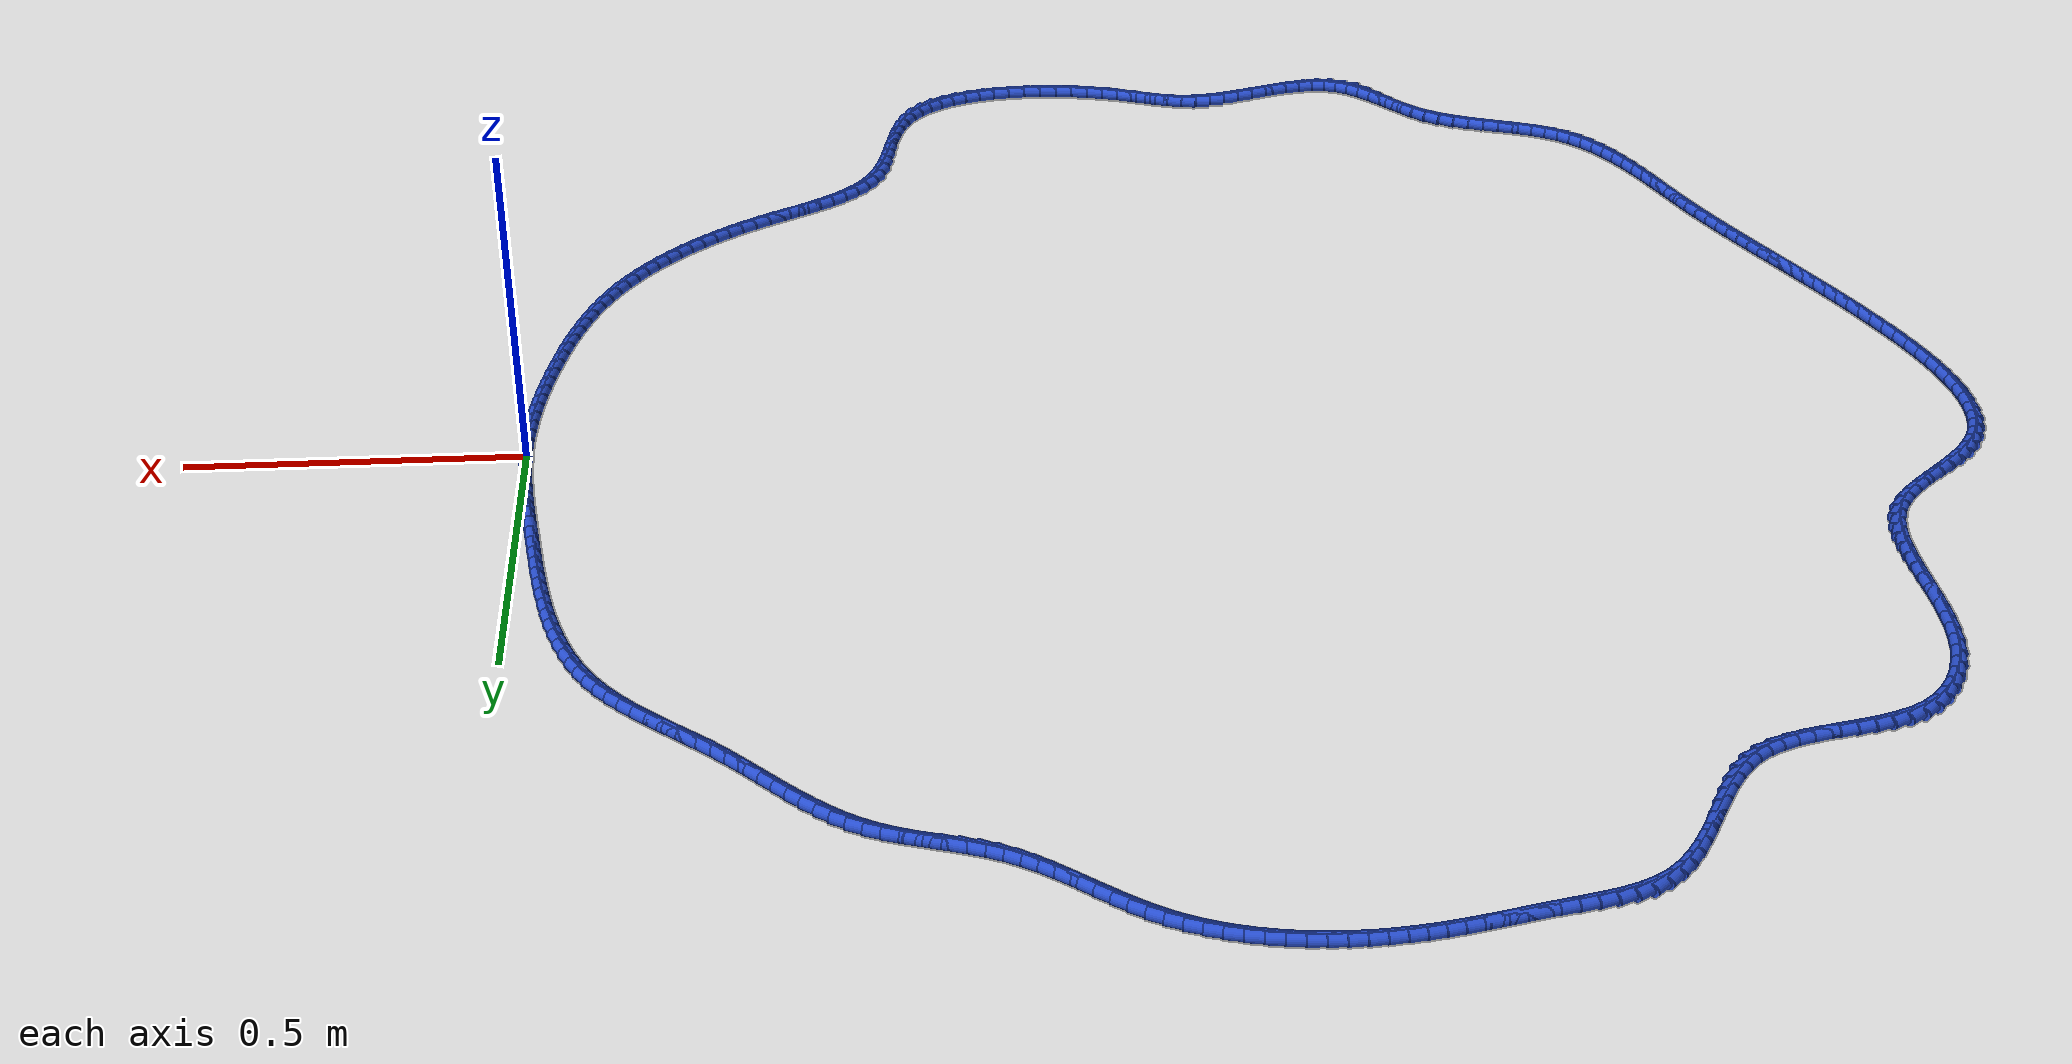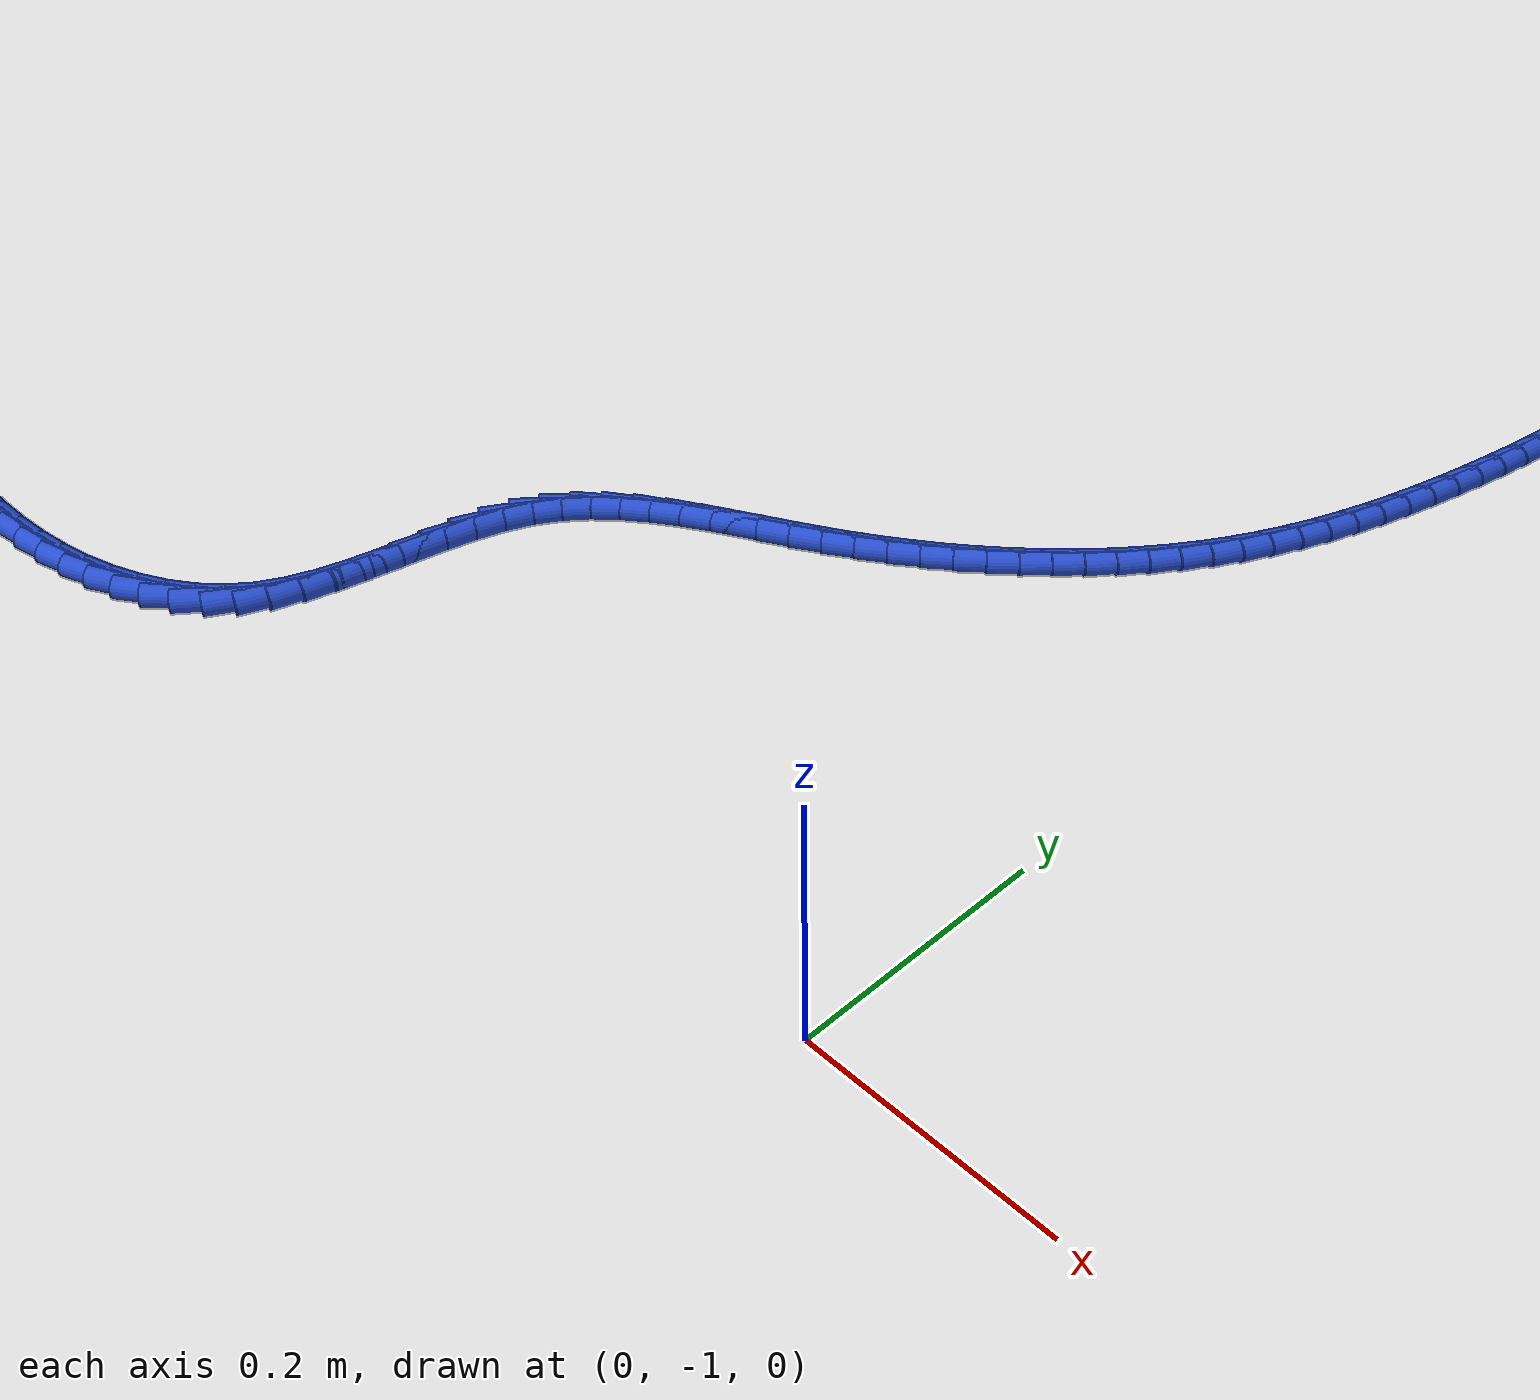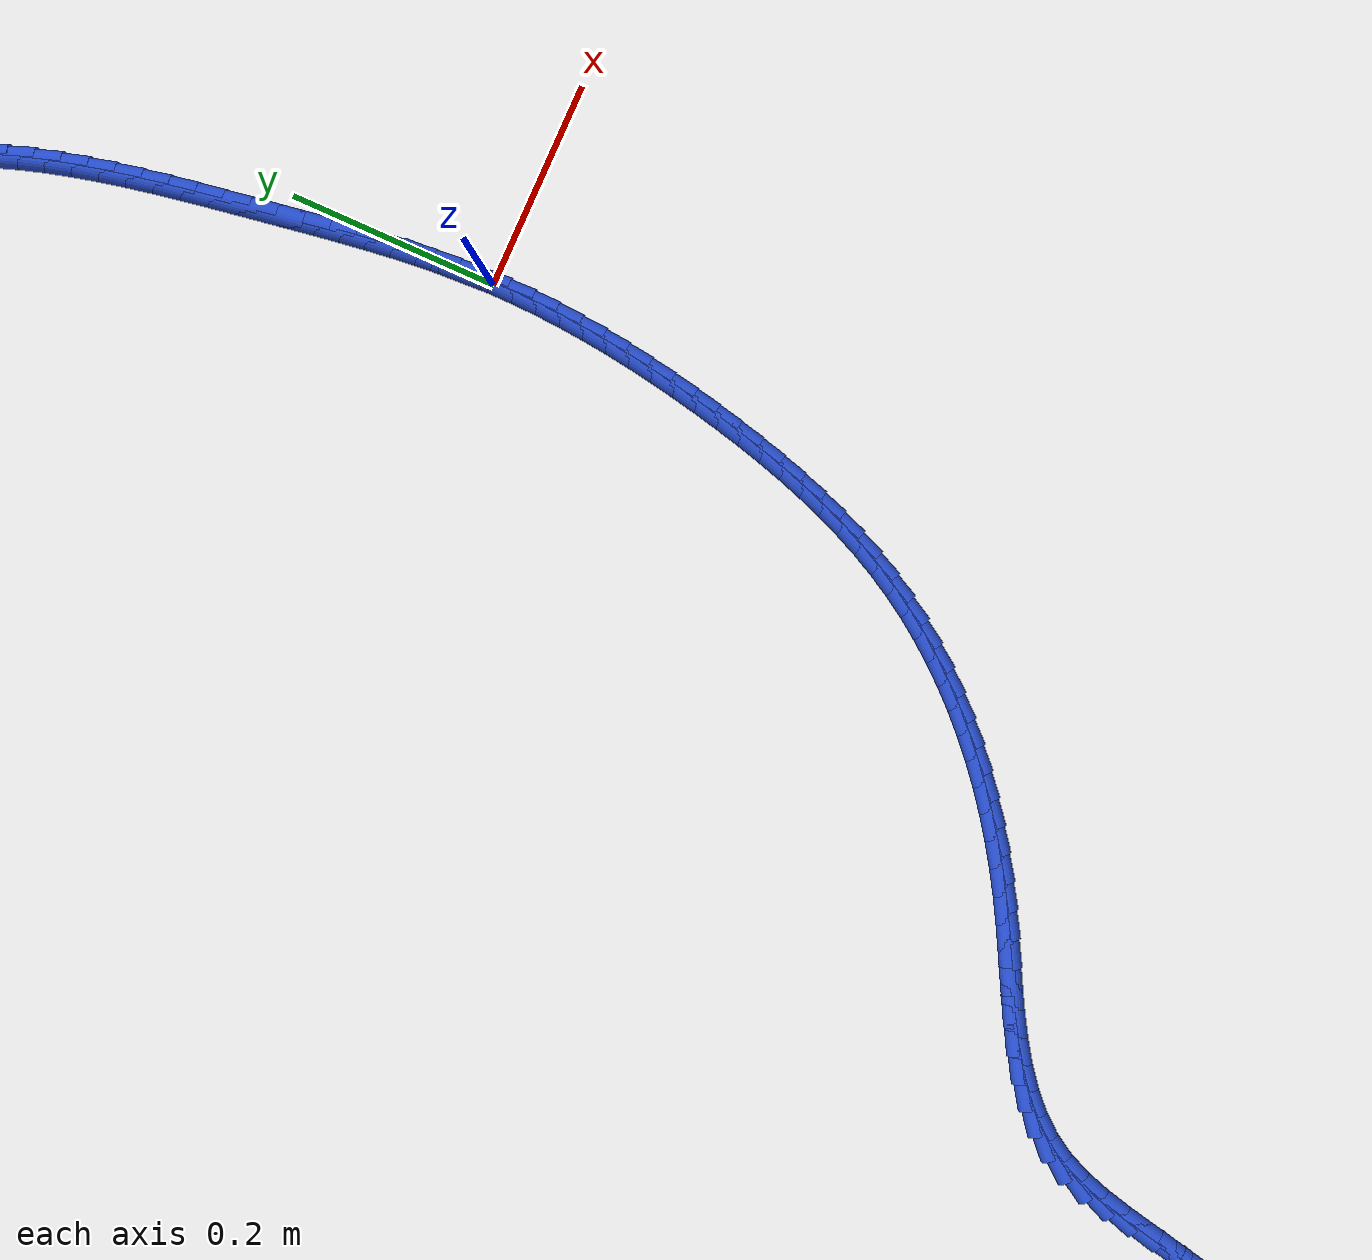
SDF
<sdf version="1.6">
 <world name="default">
  <light name="sun" type="directional">
   <pose>0 0 10 0 -0 0</pose>
   <diffuse>0.8 0.8 0.8 1</diffuse>
   <specular>0.2 0.2 0.2 1</specular>
   <attenuation>
    <range>1000</range>
    <constant>0.9</constant>
    <linear>0.01</linear>
    <quadratic>0.001</quadratic>
   </attenuation>
   <direction>-0.5 0.1 -0.9</direction>
  </light>
  <model name="ground_plane">
   <static>1</static>
   <link name="link">
    <collision name="collision">
     <geometry><plane><normal>0 0 1</normal><size>100 100</size></plane></geometry>
     <surface><friction><ode><mu>100</mu><mu2>50</mu2></ode></friction></surface>
    </collision>
    <visual name="visual">
     <cast_shadows>0</cast_shadows>
     <geometry><plane><normal>0 0 1</normal><size>100 100</size></plane></geometry>
     <material>
      <script><uri>file://media/materials/scripts/gazebo.material</uri><name>Gazebo/WhiteGlow</name></script>
     </material>
    </visual>
   </link>
  </model>
  <gravity>0 0 -9.8</gravity>
  <magnetic_field>6e-06 2.3e-05 -4.2e-05</magnetic_field>
  <atmosphere type="adiabatic"/>
  <physics name="default_physics" default="0" type="ode">
   <max_step_size>0.001</max_step_size>
   <real_time_factor>1</real_time_factor>
   <real_time_update_rate>1000</real_time_update_rate>
  </physics>
  <scene><ambient>0.4 0.4 0.4 1</ambient><background>0.7 0.7 0.7 1</background><shadows>1</shadows></scene>
  <spherical_coordinates>
   <surface_model>EARTH_WGS84</surface_model>
   <latitude_deg>0</latitude_deg>
   <longitude_deg>0</longitude_deg>
   <elevation>0</elevation>
   <heading_deg>0</heading_deg>
  </spherical_coordinates>
  <model name="line">
   <link name="link_0">
    <pose>1.8214596497756474e-17 -6.938893903907228e-18 0.01 0 1.57 -1.5419551976238133</pose>
    <collision name="collision">
     <geometry><cylinder><radius>0.01</radius><length>0.08</length></cylinder></geometry>
    </collision>
    <visual name="visual">
     <material>
      <script><name>Gazebo/Blue</name><uri>file://media/materials/scripts/gazebo.material</uri></script>
     </material>
     <geometry><cylinder><radius>0.01</radius><length>0.08</length></cylinder></geometry>
    </visual>
   </link>
   <link name="link_1">
    <pose>-0.0006937162261053146 0.024046349380320735 0.01 0 1.57 -1.512819999949289</pose>
    <collision name="collision">
     <geometry><cylinder><radius>0.01</radius><length>0.08</length></cylinder></geometry>
    </collision>
    <visual name="visual">
     <material>
      <script><name>Gazebo/Blue</name><uri>file://media/materials/scripts/gazebo.material</uri></script>
     </material>
     <geometry><cylinder><radius>0.01</radius><length>0.08</length></cylinder></geometry>
    </visual>
   </link>
   <link name="link_2">
    <pose>-0.0020873078101280047 0.04805666366629601 0.01 0 1.57 -1.48732274090152</pose>
    <collision name="collision">
     <geometry><cylinder><radius>0.01</radius><length>0.08</length></cylinder></geometry>
    </collision>
    <visual name="visual">
     <material>
      <script><name>Gazebo/Blue</name><uri>file://media/materials/scripts/gazebo.material</uri></script>
     </material>
     <geometry><cylinder><radius>0.01</radius><length>0.08</length></cylinder></geometry>
    </visual>
   </link>
   <link name="link_3">
    <pose>-0.004095669634511011 0.07206060439820915 0.01 0 1.57 -1.4655553132035113</pose>
    <collision name="collision">
     <geometry><cylinder><radius>0.01</radius><length>0.08</length></cylinder></geometry>
    </collision>
    <visual name="visual">
     <material>
      <script><name>Gazebo/Blue</name><uri>file://media/materials/scripts/gazebo.material</uri></script>
     </material>
     <geometry><cylinder><radius>0.01</radius><length>0.08</length></cylinder></geometry>
    </visual>
   </link>
   <link name="link_4">
    <pose>-0.0066336965816972925 0.09608783311634343 0.01 0 1.57 -1.4475632933500446</pose>
    <collision name="collision">
     <geometry><cylinder><radius>0.01</radius><length>0.08</length></cylinder></geometry>
    </collision>
    <visual name="visual">
     <material>
      <script><name>Gazebo/Blue</name><uri>file://media/materials/scripts/gazebo.material</uri></script>
     </material>
     <geometry><cylinder><radius>0.01</radius><length>0.08</length></cylinder></geometry>
    </visual>
   </link>
   <link name="link_5">
    <pose>-0.009616283534129813 0.1201680113609822 0.01 0 1.57 -1.4333547705873702</pose>
    <collision name="collision">
     <geometry><cylinder><radius>0.01</radius><length>0.08</length></cylinder></geometry>
    </collision>
    <visual name="visual">
     <material>
      <script><name>Gazebo/Blue</name><uri>file://media/materials/scripts/gazebo.material</uri></script>
     </material>
     <geometry><cylinder><radius>0.01</radius><length>0.08</length></cylinder></geometry>
    </visual>
   </link>
   <link name="link_6">
    <pose>-0.012958325374251534 0.1443308006724088 0.01 0 1.57 -1.4229083998762917</pose>
    <collision name="collision">
     <geometry><cylinder><radius>0.01</radius><length>0.08</length></cylinder></geometry>
    </collision>
    <visual name="visual">
     <material>
      <script><name>Gazebo/Blue</name><uri>file://media/materials/scripts/gazebo.material</uri></script>
     </material>
     <geometry><cylinder><radius>0.01</radius><length>0.08</length></cylinder></geometry>
    </visual>
   </link>
   <link name="link_7">
    <pose>-0.016574716984505404 0.16860586259090637 0.01 0 1.57 -1.4161801827466063</pose>
    <collision name="collision">
     <geometry><cylinder><radius>0.01</radius><length>0.08</length></cylinder></geometry>
    </collision>
    <visual name="visual">
     <material>
      <script><name>Gazebo/Blue</name><uri>file://media/materials/scripts/gazebo.material</uri></script>
     </material>
     <geometry><cylinder><radius>0.01</radius><length>0.08</length></cylinder></geometry>
    </visual>
   </link>
   <link name="link_8">
    <pose>-0.0203803532473344 0.19302285865675836 0.01 0 1.57 -1.4131087303598602</pose>
    <collision name="collision">
     <geometry><cylinder><radius>0.01</radius><length>0.08</length></cylinder></geometry>
    </collision>
    <visual name="visual">
     <material>
      <script><name>Gazebo/Blue</name><uri>file://media/materials/scripts/gazebo.material</uri></script>
     </material>
     <geometry><cylinder><radius>0.01</radius><length>0.08</length></cylinder></geometry>
    </visual>
   </link>
   <link name="link_9">
    <pose>-0.024290129045181463 0.21761145041024801 0.01 0 1.57 -1.4129529285050118</pose>
    <collision name="collision">
     <geometry><cylinder><radius>0.01</radius><length>0.08</length></cylinder></geometry>
    </collision>
    <visual name="visual">
     <material>
      <script><name>Gazebo/Blue</name><uri>file://media/materials/scripts/gazebo.material</uri></script>
     </material>
     <geometry><cylinder><radius>0.01</radius><length>0.08</length></cylinder></geometry>
    </visual>
   </link>
   <link name="link_10">
    <pose>-0.028234325391510363 0.24239161802522363 0.01 0 1.57 -1.4107768913329715</pose>
    <collision name="collision">
     <geometry><cylinder><radius>0.01</radius><length>0.08</length></cylinder></geometry>
    </collision>
    <visual name="visual">
     <material>
      <script><name>Gazebo/Blue</name><uri>file://media/materials/scripts/gazebo.material</uri></script>
     </material>
     <geometry><cylinder><radius>0.01</radius><length>0.08</length></cylinder></geometry>
    </visual>
   </link>
   <link name="link_11">
    <pose>-0.032256473338777486 0.26731208171259724 0.01 0 1.57 -1.4044299498013033</pose>
    <collision name="collision">
     <geometry><cylinder><radius>0.01</radius><length>0.08</length></cylinder></geometry>
    </collision>
    <visual name="visual">
     <material>
      <script><name>Gazebo/Blue</name><uri>file://media/materials/scripts/gazebo.material</uri></script>
     </material>
     <geometry><cylinder><radius>0.01</radius><length>0.08</length></cylinder></geometry>
    </visual>
   </link>
   <link name="link_12">
    <pose>-0.03645068229982774 0.2922897364219504 0.01 0 1.57 -1.3938943493233702</pose>
    <collision name="collision">
     <geometry><cylinder><radius>0.01</radius><length>0.08</length></cylinder></geometry>
    </collision>
    <visual name="visual">
     <material>
      <script><name>Gazebo/Blue</name><uri>file://media/materials/scripts/gazebo.material</uri></script>
     </material>
     <geometry><cylinder><radius>0.01</radius><length>0.08</length></cylinder></geometry>
    </visual>
   </link>
   <link name="link_13">
    <pose>-0.04091129641893349 0.3172413294035526 0.01 0 1.57 -1.379100509054995</pose>
    <collision name="collision">
     <geometry><cylinder><radius>0.01</radius><length>0.08</length></cylinder></geometry>
    </collision>
    <visual name="visual">
     <material>
      <script><name>Gazebo/Blue</name><uri>file://media/materials/scripts/gazebo.material</uri></script>
     </material>
     <geometry><cylinder><radius>0.01</radius><length>0.08</length></cylinder></geometry>
    </visual>
   </link>
   <link name="link_14">
    <pose>-0.04573265984036708 0.3420836079076735 0.01 0 1.57 -1.3599211486053158</pose>
    <collision name="collision">
     <geometry><cylinder><radius>0.01</radius><length>0.08</length></cylinder></geometry>
    </collision>
    <visual name="visual">
     <material>
      <script><name>Gazebo/Blue</name><uri>file://media/materials/scripts/gazebo.material</uri></script>
     </material>
     <geometry><cylinder><radius>0.01</radius><length>0.08</length></cylinder></geometry>
    </visual>
   </link>
   <link name="link_15">
    <pose>-0.051009116708400894 0.3667333191845827 0.01 0 1.57 -1.3361763557070856</pose>
    <collision name="collision">
     <geometry><cylinder><radius>0.01</radius><length>0.08</length></cylinder></geometry>
    </collision>
    <visual name="visual">
     <material>
      <script><name>Gazebo/Blue</name><uri>file://media/materials/scripts/gazebo.material</uri></script>
     </material>
     <geometry><cylinder><radius>0.01</radius><length>0.08</length></cylinder></geometry>
    </visual>
   </link>
   <link name="link_16">
    <pose>-0.05683501116730728 0.3911072104845499 0.01 0 1.57 -1.3076405448271664</pose>
    <collision name="collision">
     <geometry><cylinder><radius>0.01</radius><length>0.08</length></cylinder></geometry>
    </collision>
    <visual name="visual">
     <material>
      <script><name>Gazebo/Blue</name><uri>file://media/materials/scripts/gazebo.material</uri></script>
     </material>
     <geometry><cylinder><radius>0.01</radius><length>0.08</length></cylinder></geometry>
    </visual>
   </link>
   <link name="link_17">
    <pose>-0.06330468736135858 0.41512202905784457 0.01 0 1.57 -1.274052811666725</pose>
    <collision name="collision">
     <geometry><cylinder><radius>0.01</radius><length>0.08</length></cylinder></geometry>
    </collision>
    <visual name="visual">
     <material>
      <script><name>Gazebo/Blue</name><uri>file://media/materials/scripts/gazebo.material</uri></script>
     </material>
     <geometry><cylinder><radius>0.01</radius><length>0.08</length></cylinder></geometry>
    </visual>
   </link>
   <link name="link_18">
    <pose>-0.07051248943482716 0.43869452215473653 0.01 0 1.57 -1.2351326086215708</pose>
    <collision name="collision">
     <geometry><cylinder><radius>0.01</radius><length>0.08</length></cylinder></geometry>
    </collision>
    <visual name="visual">
     <material>
      <script><name>Gazebo/Blue</name><uri>file://media/materials/scripts/gazebo.material</uri></script>
     </material>
     <geometry><cylinder><radius>0.01</radius><length>0.08</length></cylinder></geometry>
    </visual>
   </link>
   <link name="link_19">
    <pose>-0.07855276153198539 0.4617414370254953 0.01 0 1.57 -1.1906030070549383</pose>
    <collision name="collision">
     <geometry><cylinder><radius>0.01</radius><length>0.08</length></cylinder></geometry>
    </collision>
    <visual name="visual">
     <material>
      <script><name>Gazebo/Blue</name><uri>file://media/materials/scripts/gazebo.material</uri></script>
     </material>
     <geometry><cylinder><radius>0.01</radius><length>0.08</length></cylinder></geometry>
    </visual>
   </link>
   <link name="link_20">
    <pose>-0.08751984779710562 0.4841795209203905 0.01 0 1.57 -1.1402238413276138</pose>
    <collision name="collision">
     <geometry><cylinder><radius>0.01</radius><length>0.08</length></cylinder></geometry>
    </collision>
    <visual name="visual">
     <material>
      <script><name>Gazebo/Blue</name><uri>file://media/materials/scripts/gazebo.material</uri></script>
     </material>
     <geometry><cylinder><radius>0.01</radius><length>0.08</length></cylinder></geometry>
    </visual>
   </link>
   <link name="link_21">
    <pose>-0.0975080923744602 0.5059255210896917 0.01 0 1.57 -1.0838363495774999</pose>
    <collision name="collision">
     <geometry><cylinder><radius>0.01</radius><length>0.08</length></cylinder></geometry>
    </collision>
    <visual name="visual">
     <material>
      <script><name>Gazebo/Blue</name><uri>file://media/materials/scripts/gazebo.material</uri></script>
     </material>
     <geometry><cylinder><radius>0.01</radius><length>0.08</length></cylinder></geometry>
    </visual>
   </link>
   <link name="link_22">
    <pose>-0.1086118394083215 0.5268961847836685 0.01 0 1.57 -1.021418997509908</pose>
    <collision name="collision">
     <geometry><cylinder><radius>0.01</radius><length>0.08</length></cylinder></geometry>
    </collision>
    <visual name="visual">
     <material>
      <script><name>Gazebo/Blue</name><uri>file://media/materials/scripts/gazebo.material</uri></script>
     </material>
     <geometry><cylinder><radius>0.01</radius><length>0.08</length></cylinder></geometry>
    </visual>
   </link>
   <link name="link_23">
    <pose>-0.12092543304296191 0.5470082592525907 0.01 0 1.57 -0.9531505050022364</pose>
    <collision name="collision">
     <geometry><cylinder><radius>0.01</radius><length>0.08</length></cylinder></geometry>
    </collision>
    <visual name="visual">
     <material>
      <script><name>Gazebo/Blue</name><uri>file://media/materials/scripts/gazebo.material</uri></script>
     </material>
     <geometry><cylinder><radius>0.01</radius><length>0.08</length></cylinder></geometry>
    </visual>
   </link>
   <link name="link_24">
    <pose>-0.13454321742265374 0.5661784917467279 0.01 0 1.57 -0.8811180825184841</pose>
    <collision name="collision">
     <geometry><cylinder><radius>0.01</radius><length>0.08</length></cylinder></geometry>
    </collision>
    <visual name="visual">
     <material>
      <script><name>Gazebo/Blue</name><uri>file://media/materials/scripts/gazebo.material</uri></script>
     </material>
     <geometry><cylinder><radius>0.01</radius><length>0.08</length></cylinder></geometry>
    </visual>
   </link>
   <link name="link_25">
    <pose>-0.14953015879634676 0.584348989343192 0.01 0 1.57 -0.8166576979792909</pose>
    <collision name="collision">
     <geometry><cylinder><radius>0.01</radius><length>0.08</length></cylinder></geometry>
    </collision>
    <visual name="visual">
     <material>
      <script><name>Gazebo/Blue</name><uri>file://media/materials/scripts/gazebo.material</uri></script>
     </material>
     <geometry><cylinder><radius>0.01</radius><length>0.08</length></cylinder></geometry>
    </visual>
   </link>
   <link name="link_26">
    <pose>-0.165760170861291 0.6016267810638343 0.01 0 1.57 -0.7643381814573068</pose>
    <collision name="collision">
     <geometry><cylinder><radius>0.01</radius><length>0.08</length></cylinder></geometry>
    </collision>
    <visual name="visual">
     <material>
      <script><name>Gazebo/Blue</name><uri>file://media/materials/scripts/gazebo.material</uri></script>
     </material>
     <geometry><cylinder><radius>0.01</radius><length>0.08</length></cylinder></geometry>
    </visual>
   </link>
   <link name="link_27">
    <pose>-0.1830307702176456 0.618184844056886 0.01 0 1.57 -0.7240153133828903</pose>
    <collision name="collision">
     <geometry><cylinder><radius>0.01</radius><length>0.08</length></cylinder></geometry>
    </collision>
    <visual name="visual">
     <material>
      <script><name>Gazebo/Blue</name><uri>file://media/materials/scripts/gazebo.material</uri></script>
     </material>
     <geometry><cylinder><radius>0.01</radius><length>0.08</length></cylinder></geometry>
    </visual>
   </link>
   <link name="link_28">
    <pose>-0.20113927200312362 0.6341963293786358 0.01 0 1.57 -0.6953139591990553</pose>
    <collision name="collision">
     <geometry><cylinder><radius>0.01</radius><length>0.08</length></cylinder></geometry>
    </collision>
    <visual name="visual">
     <material>
      <script><name>Gazebo/Blue</name><uri>file://media/materials/scripts/gazebo.material</uri></script>
     </material>
     <geometry><cylinder><radius>0.01</radius><length>0.08</length></cylinder></geometry>
    </visual>
   </link>
   <link name="link_29">
    <pose>-0.21988299135543846 0.6498343880853736 0.01 0 1.57 -0.677810780749041</pose>
    <collision name="collision">
     <geometry><cylinder><radius>0.01</radius><length>0.08</length></cylinder></geometry>
    </collision>
    <visual name="visual">
     <material>
      <script><name>Gazebo/Blue</name><uri>file://media/materials/scripts/gazebo.material</uri></script>
     </material>
     <geometry><cylinder><radius>0.01</radius><length>0.08</length></cylinder></geometry>
    </visual>
   </link>
   <link name="link_30">
    <pose>-0.23905924341230292 0.6652721712333888 0.01 0 1.57 -0.6711416945893081</pose>
    <collision name="collision">
     <geometry><cylinder><radius>0.01</radius><length>0.08</length></cylinder></geometry>
    </collision>
    <visual name="visual">
     <material>
      <script><name>Gazebo/Blue</name><uri>file://media/materials/scripts/gazebo.material</uri></script>
     </material>
     <geometry><cylinder><radius>0.01</radius><length>0.08</length></cylinder></geometry>
    </visual>
   </link>
   <link name="link_31">
    <pose>-0.2584653433114304 0.680682829878971 0.01 0 1.57 -0.6750569815832442</pose>
    <collision name="collision">
     <geometry><cylinder><radius>0.01</radius><length>0.08</length></cylinder></geometry>
    </collision>
    <visual name="visual">
     <material>
      <script><name>Gazebo/Blue</name><uri>file://media/materials/scripts/gazebo.material</uri></script>
     </material>
     <geometry><cylinder><radius>0.01</radius><length>0.08</length></cylinder></geometry>
    </visual>
   </link>
   <link name="link_32">
    <pose>-0.2778986061905339 0.6962395150784098 0.01 0 1.57 -0.689436163016285</pose>
    <collision name="collision">
     <geometry><cylinder><radius>0.01</radius><length>0.08</length></cylinder></geometry>
    </collision>
    <visual name="visual">
     <material>
      <script><name>Gazebo/Blue</name><uri>file://media/materials/scripts/gazebo.material</uri></script>
     </material>
     <geometry><cylinder><radius>0.01</radius><length>0.08</length></cylinder></geometry>
    </visual>
   </link>
   <link name="link_33">
    <pose>-0.2971563471873267 0.7121153778879944 0.01 0 1.57 -0.7140899568409086</pose>
    <collision name="collision">
     <geometry><cylinder><radius>0.01</radius><length>0.08</length></cylinder></geometry>
    </collision>
    <visual name="visual">
     <material>
      <script><name>Gazebo/Blue</name><uri>file://media/materials/scripts/gazebo.material</uri></script>
     </material>
     <geometry><cylinder><radius>0.01</radius><length>0.08</length></cylinder></geometry>
    </visual>
   </link>
   <link name="link_34">
    <pose>-0.3160388248367355 0.7284801673239301 0.01 0 1.57 -0.740562881369543</pose>
    <collision name="collision">
     <geometry><cylinder><radius>0.01</radius><length>0.08</length></cylinder></geometry>
    </collision>
    <visual name="visual">
     <material>
      <script><name>Gazebo/Blue</name><uri>file://media/materials/scripts/gazebo.material</uri></script>
     </material>
     <geometry><cylinder><radius>0.01</radius><length>0.08</length></cylinder></geometry>
    </visual>
   </link>
   <link name="link_35">
    <pose>-0.33448552711817664 0.7453427080973823 0.01 0 1.57 -0.756917644604557</pose>
    <collision name="collision">
     <geometry><cylinder><radius>0.01</radius><length>0.08</length></cylinder></geometry>
    </collision>
    <visual name="visual">
     <material>
      <script><name>Gazebo/Blue</name><uri>file://media/materials/scripts/gazebo.material</uri></script>
     </material>
     <geometry><cylinder><radius>0.01</radius><length>0.08</length></cylinder></geometry>
    </visual>
   </link>
   <link name="link_36">
    <pose>-0.3526326278672488 0.7624844912916813 0.01 0 1.57 -0.7622892568804119</pose>
    <collision name="collision">
     <geometry><cylinder><radius>0.01</radius><length>0.08</length></cylinder></geometry>
    </collision>
    <visual name="visual">
     <material>
      <script><name>Gazebo/Blue</name><uri>file://media/materials/scripts/gazebo.material</uri></script>
     </material>
     <geometry><cylinder><radius>0.01</radius><length>0.08</length></cylinder></geometry>
    </visual>
   </link>
   <link name="link_37">
    <pose>-0.37063116729618645 0.7796698251209919 0.01 0 1.57 -0.7566063400374159</pose>
    <collision name="collision">
     <geometry><cylinder><radius>0.01</radius><length>0.08</length></cylinder></geometry>
    </collision>
    <visual name="visual">
     <material>
      <script><name>Gazebo/Blue</name><uri>file://media/materials/scripts/gazebo.material</uri></script>
     </material>
     <geometry><cylinder><radius>0.01</radius><length>0.08</length></cylinder></geometry>
    </visual>
   </link>
   <link name="link_38">
    <pose>-0.3886321856172238 0.7966630177994796 0.01 0 1.57 -0.7396587050464527</pose>
    <collision name="collision">
     <geometry><cylinder><radius>0.01</radius><length>0.08</length></cylinder></geometry>
    </collision>
    <visual name="visual">
     <material>
      <script><name>Gazebo/Blue</name><uri>file://media/materials/scripts/gazebo.material</uri></script>
     </material>
     <geometry><cylinder><radius>0.01</radius><length>0.08</length></cylinder></geometry>
    </visual>
   </link>
   <link name="link_39">
    <pose>-0.4067867230425957 0.8132283775413099 0.01 0 1.57 -0.7111115890399681</pose>
    <collision name="collision">
     <geometry><cylinder><radius>0.01</radius><length>0.08</length></cylinder></geometry>
    </collision>
    <visual name="visual">
     <material>
      <script><name>Gazebo/Blue</name><uri>file://media/materials/scripts/gazebo.material</uri></script>
     </material>
     <geometry><cylinder><radius>0.01</radius><length>0.08</length></cylinder></geometry>
    </visual>
   </link>
   <link name="link_40">
    <pose>-0.42524581978453607 0.8291302125606475 0.01 0 1.57 -0.6705639966204211</pose>
    <collision name="collision">
     <geometry><cylinder><radius>0.01</radius><length>0.08</length></cylinder></geometry>
    </collision>
    <visual name="visual">
     <material>
      <script><name>Gazebo/Blue</name><uri>file://media/materials/scripts/gazebo.material</uri></script>
     </material>
     <geometry><cylinder><radius>0.01</radius><length>0.08</length></cylinder></geometry>
    </visual>
   </link>
   <link name="link_41">
    <pose>-0.44416051605527956 0.8441328310716576 0.01 0 1.57 -0.6176633760938435</pose>
    <collision name="collision">
     <geometry><cylinder><radius>0.01</radius><length>0.08</length></cylinder></geometry>
    </collision>
    <visual name="visual">
     <material>
      <script><name>Gazebo/Blue</name><uri>file://media/materials/scripts/gazebo.material</uri></script>
     </material>
     <geometry><cylinder><radius>0.01</radius><length>0.08</length></cylinder></geometry>
    </visual>
   </link>
   <link name="link_42">
    <pose>-0.4636818520670607 0.8580005412885058 0.01 0 1.57 -0.5522883748226314</pose>
    <collision name="collision">
     <geometry><cylinder><radius>0.01</radius><length>0.08</length></cylinder></geometry>
    </collision>
    <visual name="visual">
     <material>
      <script><name>Gazebo/Blue</name><uri>file://media/materials/scripts/gazebo.material</uri></script>
     </material>
     <geometry><cylinder><radius>0.01</radius><length>0.08</length></cylinder></geometry>
    </visual>
   </link>
   <link name="link_43">
    <pose>-0.4839608680321136 0.8704976514253568 0.01 0 1.57 -0.4747967986765887</pose>
    <collision name="collision">
     <geometry><cylinder><radius>0.01</radius><length>0.08</length></cylinder></geometry>
    </collision>
    <visual name="visual">
     <material>
      <script><name>Gazebo/Blue</name><uri>file://media/materials/scripts/gazebo.material</uri></script>
     </material>
     <geometry><cylinder><radius>0.01</radius><length>0.08</length></cylinder></geometry>
    </visual>
   </link>
   <link name="link_44">
    <pose>-0.505148604123842 0.8813884697635778 0.01 0 1.57 -0.39247734417948216</pose>
    <collision name="collision">
     <geometry><cylinder><radius>0.01</radius><length>0.08</length></cylinder></geometry>
    </collision>
    <visual name="visual">
     <material>
      <script><name>Gazebo/Blue</name><uri>file://media/materials/scripts/gazebo.material</uri></script>
     </material>
     <geometry><cylinder><radius>0.01</radius><length>0.08</length></cylinder></geometry>
    </visual>
   </link>
   <link name="link_45">
    <pose>-0.5273212125200486 0.8905669053662899 0.01 0 1.57 -0.3303107650152126</pose>
    <collision name="collision">
     <geometry><cylinder><radius>0.01</radius><length>0.08</length></cylinder></geometry>
    </collision>
    <visual name="visual">
     <material>
      <script><name>Gazebo/Blue</name><uri>file://media/materials/scripts/gazebo.material</uri></script>
     </material>
     <geometry><cylinder><radius>0.01</radius><length>0.08</length></cylinder></geometry>
    </visual>
   </link>
   <link name="link_46">
    <pose>-0.5502624832592734 0.8984328277179245 0.01 0 1.57 -0.29341472476749</pose>
    <collision name="collision">
     <geometry><cylinder><radius>0.01</radius><length>0.08</length></cylinder></geometry>
    </collision>
    <visual name="visual">
     <material>
      <script><name>Gazebo/Blue</name><uri>file://media/materials/scripts/gazebo.material</uri></script>
     </material>
     <geometry><cylinder><radius>0.01</radius><length>0.08</length></cylinder></geometry>
    </visual>
   </link>
   <link name="link_47">
    <pose>-0.5736848703679669 0.9055095600401898 0.01 0 1.57 -0.2807818260994357</pose>
    <collision name="collision">
     <geometry><cylinder><radius>0.01</radius><length>0.08</length></cylinder></geometry>
    </collision>
    <visual name="visual">
     <material>
      <script><name>Gazebo/Blue</name><uri>file://media/materials/scripts/gazebo.material</uri></script>
     </material>
     <geometry><cylinder><radius>0.01</radius><length>0.08</length></cylinder></geometry>
    </visual>
   </link>
   <link name="link_48">
    <pose>-0.5973008278725801 0.9123204255547945 0.01 0 1.57 -0.2919141352040017</pose>
    <collision name="collision">
     <geometry><cylinder><radius>0.01</radius><length>0.08</length></cylinder></geometry>
    </collision>
    <visual name="visual">
     <material>
      <script><name>Gazebo/Blue</name><uri>file://media/materials/scripts/gazebo.material</uri></script>
     </material>
     <geometry><cylinder><radius>0.01</radius><length>0.08</length></cylinder></geometry>
    </visual>
   </link>
   <link name="link_49">
    <pose>-0.6208228097995634 0.9193887474834468 0.01 0 1.57 -0.3270157027916848</pose>
    <collision name="collision">
     <geometry><cylinder><radius>0.01</radius><length>0.08</length></cylinder></geometry>
    </collision>
    <visual name="visual">
     <material>
      <script><name>Gazebo/Blue</name><uri>file://media/materials/scripts/gazebo.material</uri></script>
     </material>
     <geometry><cylinder><radius>0.01</radius><length>0.08</length></cylinder></geometry>
    </visual>
   </link>
   <link name="link_50">
    <pose>-0.6439632701753681 0.927237849047855 0.01 0 1.57 -0.386806727069559</pose>
    <collision name="collision">
     <geometry><cylinder><radius>0.01</radius><length>0.08</length></cylinder></geometry>
    </collision>
    <visual name="visual">
     <material>
      <script><name>Gazebo/Blue</name><uri>file://media/materials/scripts/gazebo.material</uri></script>
     </material>
     <geometry><cylinder><radius>0.01</radius><length>0.08</length></cylinder></geometry>
    </visual>
   </link>
   <link name="link_51">
    <pose>-0.6664346630744912 0.9363910533815369 0.01 0 1.57 -0.4648886362230707</pose>
    <collision name="collision">
     <geometry><cylinder><radius>0.01</radius><length>0.08</length></cylinder></geometry>
    </collision>
    <visual name="visual">
     <material>
      <script><name>Gazebo/Blue</name><uri>file://media/materials/scripts/gazebo.material</uri></script>
     </material>
     <geometry><cylinder><radius>0.01</radius><length>0.08</length></cylinder></geometry>
    </visual>
   </link>
   <link name="link_52">
    <pose>-0.6880306744134747 0.9472225814167777 0.01 0 1.57 -0.5334709822494902</pose>
    <collision name="collision">
     <geometry><cylinder><radius>0.01</radius><length>0.08</length></cylinder></geometry>
    </collision>
    <visual name="visual">
     <material>
      <script><name>Gazebo/Blue</name><uri>file://media/materials/scripts/gazebo.material</uri></script>
     </material>
     <geometry><cylinder><radius>0.01</radius><length>0.08</length></cylinder></geometry>
    </visual>
   </link>
   <link name="link_53">
    <pose>-0.7088617702876907 0.959525199562828 0.01 0 1.57 -0.5853380820975453</pose>
    <collision name="collision">
     <geometry><cylinder><radius>0.01</radius><length>0.08</length></cylinder></geometry>
    </collision>
    <visual name="visual">
     <material>
      <script><name>Gazebo/Blue</name><uri>file://media/materials/scripts/gazebo.material</uri></script>
     </material>
     <geometry><cylinder><radius>0.01</radius><length>0.08</length></cylinder></geometry>
    </visual>
   </link>
   <link name="link_54">
    <pose>-0.7291156258576577 0.9729499558919091 0.01 0 1.57 -0.620554885119948</pose>
    <collision name="collision">
     <geometry><cylinder><radius>0.01</radius><length>0.08</length></cylinder></geometry>
    </collision>
    <visual name="visual">
     <material>
      <script><name>Gazebo/Blue</name><uri>file://media/materials/scripts/gazebo.material</uri></script>
     </material>
     <geometry><cylinder><radius>0.01</radius><length>0.08</length></cylinder></geometry>
    </visual>
   </link>
   <link name="link_55">
    <pose>-0.7489799162838935 0.9871478984762427 0.01 0 1.57 -0.6394323309043143</pose>
    <collision name="collision">
     <geometry><cylinder><radius>0.01</radius><length>0.08</length></cylinder></geometry>
    </collision>
    <visual name="visual">
     <material>
      <script><name>Gazebo/Blue</name><uri>file://media/materials/scripts/gazebo.material</uri></script>
     </material>
     <geometry><cylinder><radius>0.01</radius><length>0.08</length></cylinder></geometry>
    </visual>
   </link>
   <link name="link_56">
    <pose>-0.7686423167269157 1.0017700753880499 0.01 0 1.57 -0.642239997972152</pose>
    <collision name="collision">
     <geometry><cylinder><radius>0.01</radius><length>0.08</length></cylinder></geometry>
    </collision>
    <visual name="visual">
     <material>
      <script><name>Gazebo/Blue</name><uri>file://media/materials/scripts/gazebo.material</uri></script>
     </material>
     <geometry><cylinder><radius>0.01</radius><length>0.08</length></cylinder></geometry>
    </visual>
   </link>
   <link name="link_57">
    <pose>-0.7882905023472426 1.0164675346995524 0.01 0 1.57 -0.6290617705314179</pose>
    <collision name="collision">
     <geometry><cylinder><radius>0.01</radius><length>0.08</length></cylinder></geometry>
    </collision>
    <visual name="visual">
     <material>
      <script><name>Gazebo/Blue</name><uri>file://media/materials/scripts/gazebo.material</uri></script>
     </material>
     <geometry><cylinder><radius>0.01</radius><length>0.08</length></cylinder></geometry>
    </visual>
   </link>
   <link name="link_58">
    <pose>-0.808112148305392 1.0308913244829718 0.01 0 1.57 -0.5997766941632872</pose>
    <collision name="collision">
     <geometry><cylinder><radius>0.01</radius><length>0.08</length></cylinder></geometry>
    </collision>
    <visual name="visual">
     <material>
      <script><name>Gazebo/Blue</name><uri>file://media/materials/scripts/gazebo.material</uri></script>
     </material>
     <geometry><cylinder><radius>0.01</radius><length>0.08</length></cylinder></geometry>
    </visual>
   </link>
   <link name="link_59">
    <pose>-0.8282949297618812 1.0446924928105292 0.01 0 1.57 -0.5541593537986568</pose>
    <collision name="collision">
     <geometry><cylinder><radius>0.01</radius><length>0.08</length></cylinder></geometry>
    </collision>
    <visual name="visual">
     <material>
      <script><name>Gazebo/Blue</name><uri>file://media/materials/scripts/gazebo.material</uri></script>
     </material>
     <geometry><cylinder><radius>0.01</radius><length>0.08</length></cylinder></geometry>
    </visual>
   </link>
   <link name="link_60">
    <pose>-0.8490265218772292 1.0575220877544464 0.01 0 1.57 -0.4926872468066488</pose>
    <collision name="collision">
     <geometry><cylinder><radius>0.01</radius><length>0.08</length></cylinder></geometry>
    </collision>
    <visual name="visual">
     <material>
      <script><name>Gazebo/Blue</name><uri>file://media/materials/scripts/gazebo.material</uri></script>
     </material>
     <geometry><cylinder><radius>0.01</radius><length>0.08</length></cylinder></geometry>
    </visual>
   </link>
   <link name="link_61">
    <pose>-0.870486398023129 1.0690427125179196 0.01 0 1.57 -0.42581483931830555</pose>
    <collision name="collision">
     <geometry><cylinder><radius>0.01</radius><length>0.08</length></cylinder></geometry>
    </collision>
    <visual name="visual">
     <material>
      <script><name>Gazebo/Blue</name><uri>file://media/materials/scripts/gazebo.material</uri></script>
     </material>
     <geometry><cylinder><radius>0.01</radius><length>0.08</length></cylinder></geometry>
    </visual>
   </link>
   <link name="link_62">
    <pose>-0.8927085629435945 1.0791219145037056 0.01 0 1.57 -0.3624491934970863</pose>
    <collision name="collision">
     <geometry><cylinder><radius>0.01</radius><length>0.08</length></cylinder></geometry>
    </collision>
    <visual name="visual">
     <material>
      <script><name>Gazebo/Blue</name><uri>file://media/materials/scripts/gazebo.material</uri></script>
     </material>
     <geometry><cylinder><radius>0.01</radius><length>0.08</length></cylinder></geometry>
    </visual>
   </link>
   <link name="link_63">
    <pose>-0.9156021313994316 1.0878031929885184 0.01 0 1.57 -0.30281437556361046</pose>
    <collision name="collision">
     <geometry><cylinder><radius>0.01</radius><length>0.08</length></cylinder></geometry>
    </collision>
    <visual name="visual">
     <material>
      <script><name>Gazebo/Blue</name><uri>file://media/materials/scripts/gazebo.material</uri></script>
     </material>
     <geometry><cylinder><radius>0.01</radius><length>0.08</length></cylinder></geometry>
    </visual>
   </link>
   <link name="link_64">
    <pose>-0.9390721621305026 1.0951357615943462 0.01 0 1.57 -0.24675339543639713</pose>
    <collision name="collision">
     <geometry><cylinder><radius>0.01</radius><length>0.08</length></cylinder></geometry>
    </collision>
    <visual name="visual">
     <material>
      <script><name>Gazebo/Blue</name><uri>file://media/materials/scripts/gazebo.material</uri></script>
     </material>
     <geometry><cylinder><radius>0.01</radius><length>0.08</length></cylinder></geometry>
    </visual>
   </link>
   <link name="link_65">
    <pose>-0.9630237138766709 1.1011688339431802 0.01 0 1.57 -0.1940416436659456</pose>
    <collision name="collision">
     <geometry><cylinder><radius>0.01</radius><length>0.08</length></cylinder></geometry>
    </collision>
    <visual name="visual">
     <material>
      <script><name>Gazebo/Blue</name><uri>file://media/materials/scripts/gazebo.material</uri></script>
     </material>
     <geometry><cylinder><radius>0.01</radius><length>0.08</length></cylinder></geometry>
    </visual>
   </link>
   <link name="link_66">
    <pose>-0.987361845377799 1.1059516236570102 0.01 0 1.57 -0.14441011614494112</pose>
    <collision name="collision">
     <geometry><cylinder><radius>0.01</radius><length>0.08</length></cylinder></geometry>
    </collision>
    <visual name="visual">
     <material>
      <script><name>Gazebo/Blue</name><uri>file://media/materials/scripts/gazebo.material</uri></script>
     </material>
     <geometry><cylinder><radius>0.01</radius><length>0.08</length></cylinder></geometry>
    </visual>
   </link>
   <link name="link_67">
    <pose>-1.0119916153737492 1.1095333443578241 0.01 0 1.57 -0.09756324820961994</pose>
    <collision name="collision">
     <geometry><cylinder><radius>0.01</radius><length>0.08</length></cylinder></geometry>
    </collision>
    <visual name="visual">
     <material>
      <script><name>Gazebo/Blue</name><uri>file://media/materials/scripts/gazebo.material</uri></script>
     </material>
     <geometry><cylinder><radius>0.01</radius><length>0.08</length></cylinder></geometry>
    </visual>
   </link>
   <link name="link_68">
    <pose>-1.036818082604385 1.1119632096676135 0.01 0 1.57 -0.053191580065725955</pose>
    <collision name="collision">
     <geometry><cylinder><radius>0.01</radius><length>0.08</length></cylinder></geometry>
    </collision>
    <visual name="visual">
     <material>
      <script><name>Gazebo/Blue</name><uri>file://media/materials/scripts/gazebo.material</uri></script>
     </material>
     <geometry><cylinder><radius>0.01</radius><length>0.08</length></cylinder></geometry>
    </visual>
   </link>
   <link name="link_69">
    <pose>-1.061746305809568 1.113290433208367 0.01 0 1.57 -0.010979906737210596</pose>
    <collision name="collision">
     <geometry><cylinder><radius>0.01</radius><length>0.08</length></cylinder></geometry>
    </collision>
    <visual name="visual">
     <material>
      <script><name>Gazebo/Blue</name><uri>file://media/materials/scripts/gazebo.material</uri></script>
     </material>
     <geometry><cylinder><radius>0.01</radius><length>0.08</length></cylinder></geometry>
    </visual>
   </link>
   <link name="link_70">
    <pose>-1.086681343729162 1.1135642286020753 0.01 0 1.57 0.02938831419144995</pose>
    <collision name="collision">
     <geometry><cylinder><radius>0.01</radius><length>0.08</length></cylinder></geometry>
    </collision>
    <visual name="visual">
     <material>
      <script><name>Gazebo/Blue</name><uri>file://media/materials/scripts/gazebo.material</uri></script>
     </material>
     <geometry><cylinder><radius>0.01</radius><length>0.08</length></cylinder></geometry>
    </visual>
   </link>
   <link name="link_71">
    <pose>-1.1115282551030292 1.1128338094707275 0.01 0 1.57 0.06822958685624986</pose>
    <collision name="collision">
     <geometry><cylinder><radius>0.01</radius><length>0.08</length></cylinder></geometry>
    </collision>
    <visual name="visual">
     <material>
      <script><name>Gazebo/Blue</name><uri>file://media/materials/scripts/gazebo.material</uri></script>
     </material>
     <geometry><cylinder><radius>0.01</radius><length>0.08</length></cylinder></geometry>
    </visual>
   </link>
   <link name="link_72">
    <pose>-1.136192098671032 1.1111483894363132 0.01 0 1.57 0.10586034858756094</pose>
    <collision name="collision">
     <geometry><cylinder><radius>0.01</radius><length>0.08</length></cylinder></geometry>
    </collision>
    <visual name="visual">
     <material>
      <script><name>Gazebo/Blue</name><uri>file://media/materials/scripts/gazebo.material</uri></script>
     </material>
     <geometry><cylinder><radius>0.01</radius><length>0.08</length></cylinder></geometry>
    </visual>
   </link>
   <link name="link_73">
    <pose>-1.16057798105714 1.1085572048921641 0.01 0 1.57 0.14148737072743675</pose>
    <collision name="collision">
     <geometry><cylinder><radius>0.01</radius><length>0.08</length></cylinder></geometry>
    </collision>
    <visual name="visual">
     <material>
      <script><name>Gazebo/Blue</name><uri>file://media/materials/scripts/gazebo.material</uri></script>
     </material>
     <geometry><cylinder><radius>0.01</radius><length>0.08</length></cylinder></geometry>
    </visual>
   </link>
   <link name="link_74">
    <pose>-1.1846352135413685 1.1051305138066885 0.01 0 1.57 0.17187351367555587</pose>
    <collision name="collision">
     <geometry><cylinder><radius>0.01</radius><length>0.08</length></cylinder></geometry>
    </collision>
    <visual name="visual">
     <material>
      <script><name>Gazebo/Blue</name><uri>file://media/materials/scripts/gazebo.material</uri></script>
     </material>
     <geometry><cylinder><radius>0.01</radius><length>0.08</length></cylinder></geometry>
    </visual>
   </link>
   <link name="link_75">
    <pose>-1.2084390975408925 1.1009984889030753 0.01 0 1.57 0.19605157910003046</pose>
    <collision name="collision">
     <geometry><cylinder><radius>0.01</radius><length>0.08</length></cylinder></geometry>
    </collision>
    <visual name="visual">
     <material>
      <script><name>Gazebo/Blue</name><uri>file://media/materials/scripts/gazebo.material</uri></script>
     </material>
     <geometry><cylinder><radius>0.01</radius><length>0.08</length></cylinder></geometry>
    </visual>
   </link>
   <link name="link_76">
    <pose>-1.2320872328492711 1.0963019069230744 0.01 0 1.57 0.21374106385140762</pose>
    <collision name="collision">
     <geometry><cylinder><radius>0.01</radius><length>0.08</length></cylinder></geometry>
    </collision>
    <visual name="visual">
     <material>
      <script><name>Gazebo/Blue</name><uri>file://media/materials/scripts/gazebo.material</uri></script>
     </material>
     <geometry><cylinder><radius>0.01</radius><length>0.08</length></cylinder></geometry>
    </visual>
   </link>
   <link name="link_77">
    <pose>-1.2556772192600638 1.091181544608437 0.01 0 1.57 0.22480574770204884</pose>
    <collision name="collision">
     <geometry><cylinder><radius>0.01</radius><length>0.08</length></cylinder></geometry>
    </collision>
    <visual name="visual">
     <material>
      <script><name>Gazebo/Blue</name><uri>file://media/materials/scripts/gazebo.material</uri></script>
     </material>
     <geometry><cylinder><radius>0.01</radius><length>0.08</length></cylinder></geometry>
    </visual>
   </link>
   <link name="link_78">
    <pose>-1.2793066565668305 1.085778178700913 0.01 0 1.57 0.22923508137789167</pose>
    <collision name="collision">
     <geometry><cylinder><radius>0.01</radius><length>0.08</length></cylinder></geometry>
    </collision>
    <visual name="visual">
     <material>
      <script><name>Gazebo/Blue</name><uri>file://media/materials/scripts/gazebo.material</uri></script>
     </material>
     <geometry><cylinder><radius>0.01</radius><length>0.08</length></cylinder></geometry>
    </visual>
   </link>
   <link name="link_79">
    <pose>-1.3030731445631303 1.0802325859422544 0.01 0 1.57 0.2271278907790946</pose>
    <collision name="collision">
     <geometry><cylinder><radius>0.01</radius><length>0.08</length></cylinder></geometry>
    </collision>
    <visual name="visual">
     <material>
      <script><name>Gazebo/Blue</name><uri>file://media/materials/scripts/gazebo.material</uri></script>
     </material>
     <geometry><cylinder><radius>0.01</radius><length>0.08</length></cylinder></geometry>
    </visual>
   </link>
   <link name="link_80">
    <pose>-1.3270742830425226 1.0746855430742113 0.01 0 1.57 0.218688241988732</pose>
    <collision name="collision">
     <geometry><cylinder><radius>0.01</radius><length>0.08</length></cylinder></geometry>
    </collision>
    <visual name="visual">
     <material>
      <script><name>Gazebo/Blue</name><uri>file://media/materials/scripts/gazebo.material</uri></script>
     </material>
     <geometry><cylinder><radius>0.01</radius><length>0.08</length></cylinder></geometry>
    </visual>
   </link>
   <link name="link_81">
    <pose>-1.351407540017005 1.0692776599089766 0.01 0 1.57 0.21147250631867012</pose>
    <collision name="collision">
     <geometry><cylinder><radius>0.01</radius><length>0.08</length></cylinder></geometry>
    </collision>
    <visual name="visual">
     <material>
      <script><name>Gazebo/Blue</name><uri>file://media/materials/scripts/gazebo.material</uri></script>
     </material>
     <geometry><cylinder><radius>0.01</radius><length>0.08</length></cylinder></geometry>
    </visual>
   </link>
   <link name="link_82">
    <pose>-1.3760434550797909 1.0639887642459527 0.01 0 1.57 0.2262716564803338</pose>
    <collision name="collision">
     <geometry><cylinder><radius>0.01</radius><length>0.08</length></cylinder></geometry>
    </collision>
    <visual name="visual">
     <material>
      <script><name>Gazebo/Blue</name><uri>file://media/materials/scripts/gazebo.material</uri></script>
     </material>
     <geometry><cylinder><radius>0.01</radius><length>0.08</length></cylinder></geometry>
    </visual>
   </link>
   <link name="link_83">
    <pose>-1.4005889251716173 1.0583380526235378 0.01 0 1.57 0.26743883328999424</pose>
    <collision name="collision">
     <geometry><cylinder><radius>0.01</radius><length>0.08</length></cylinder></geometry>
    </collision>
    <visual name="visual">
     <material>
      <script><name>Gazebo/Blue</name><uri>file://media/materials/scripts/gazebo.material</uri></script>
     </material>
     <geometry><cylinder><radius>0.01</radius><length>0.08</length></cylinder></geometry>
    </visual>
   </link>
   <link name="link_84">
    <pose>-1.4245861360449223 1.05176275100802 0.01 0 1.57 0.33728565520012355</pose>
    <collision name="collision">
     <geometry><cylinder><radius>0.01</radius><length>0.08</length></cylinder></geometry>
    </collision>
    <visual name="visual">
     <material>
      <script><name>Gazebo/Blue</name><uri>file://media/materials/scripts/gazebo.material</uri></script>
     </material>
     <geometry><cylinder><radius>0.01</radius><length>0.08</length></cylinder></geometry>
    </visual>
   </link>
   <link name="link_85">
    <pose>-1.4475772734521453 1.043700085365688 0.01 0 1.57 0.4391704914647384</pose>
    <collision name="collision">
     <geometry><cylinder><radius>0.01</radius><length>0.08</length></cylinder></geometry>
    </collision>
    <visual name="visual">
     <material>
      <script><name>Gazebo/Blue</name><uri>file://media/materials/scripts/gazebo.material</uri></script>
     </material>
     <geometry><cylinder><radius>0.01</radius><length>0.08</length></cylinder></geometry>
    </visual>
   </link>
   <link name="link_86">
    <pose>-1.469104523145725 1.03358728166283 0.01 0 1.57 0.5756615023387348</pose>
    <collision name="collision">
     <geometry><cylinder><radius>0.01</radius><length>0.08</length></cylinder></geometry>
    </collision>
    <visual name="visual">
     <material>
      <script><name>Gazebo/Blue</name><uri>file://media/materials/scripts/gazebo.material</uri></script>
     </material>
     <geometry><cylinder><radius>0.01</radius><length>0.08</length></cylinder></geometry>
    </visual>
   </link>
   <link name="link_87">
    <pose>-1.4887111086485414 1.0208628977236138 0.01 0 1.57 0.7289749240008232</pose>
    <collision name="collision">
     <geometry><cylinder><radius>0.01</radius><length>0.08</length></cylinder></geometry>
    </collision>
    <visual name="visual">
     <material>
      <script><name>Gazebo/Blue</name><uri>file://media/materials/scripts/gazebo.material</uri></script>
     </material>
     <geometry><cylinder><radius>0.01</radius><length>0.08</length></cylinder></geometry>
    </visual>
   </link>
   <link name="link_88">
    <pose>-1.5061748177729901 1.0052665274054322 0.01 0 1.57 0.8570866139012752</pose>
    <collision name="collision">
     <geometry><cylinder><radius>0.01</radius><length>0.08</length></cylinder></geometry>
    </collision>
    <visual name="visual">
     <material>
      <script><name>Gazebo/Blue</name><uri>file://media/materials/scripts/gazebo.material</uri></script>
     </material>
     <geometry><cylinder><radius>0.01</radius><length>0.08</length></cylinder></geometry>
    </visual>
   </link>
   <link name="link_89">
    <pose>-1.5218041183499629 0.9872188307587024 0.01 0 1.57 0.9538179005927426</pose>
    <collision name="collision">
     <geometry><cylinder><radius>0.01</radius><length>0.08</length></cylinder></geometry>
    </collision>
    <visual name="visual">
     <material>
      <script><name>Gazebo/Blue</name><uri>file://media/materials/scripts/gazebo.material</uri></script>
     </material>
     <geometry><cylinder><radius>0.01</radius><length>0.08</length></cylinder></geometry>
    </visual>
   </link>
   <link name="link_90">
    <pose>-1.5359804335910876 0.9672340975950672 0.01 0 1.57 1.021485286139983</pose>
    <collision name="collision">
     <geometry><cylinder><radius>0.01</radius><length>0.08</length></cylinder></geometry>
    </collision>
    <visual name="visual">
     <material>
      <script><name>Gazebo/Blue</name><uri>file://media/materials/scripts/gazebo.material</uri></script>
     </material>
     <geometry><cylinder><radius>0.01</radius><length>0.08</length></cylinder></geometry>
    </visual>
   </link>
   <link name="link_91">
    <pose>-1.5490851867079933 0.9458266177261706 0.01 0 1.57 1.0631202853963024</pose>
    <collision name="collision">
     <geometry><cylinder><radius>0.01</radius><length>0.08</length></cylinder></geometry>
    </collision>
    <visual name="visual">
     <material>
      <script><name>Gazebo/Blue</name><uri>file://media/materials/scripts/gazebo.material</uri></script>
     </material>
     <geometry><cylinder><radius>0.01</radius><length>0.08</length></cylinder></geometry>
    </visual>
   </link>
   <link name="link_92">
    <pose>-1.5614998009123093 0.9235106809636571 0.01 0 1.57 1.0810500941845627</pose>
    <collision name="collision">
     <geometry><cylinder><radius>0.01</radius><length>0.08</length></cylinder></geometry>
    </collision>
    <visual name="visual">
     <material>
      <script><name>Gazebo/Blue</name><uri>file://media/materials/scripts/gazebo.material</uri></script>
     </material>
     <geometry><cylinder><radius>0.01</radius><length>0.08</length></cylinder></geometry>
    </visual>
   </link>
   <link name="link_93">
    <pose>-1.5736056994156638 0.9008005771191699 0.01 0 1.57 1.076348227262313</pose>
    <collision name="collision">
     <geometry><cylinder><radius>0.01</radius><length>0.08</length></cylinder></geometry>
    </collision>
    <visual name="visual">
     <material>
      <script><name>Gazebo/Blue</name><uri>file://media/materials/scripts/gazebo.material</uri></script>
     </material>
     <geometry><cylinder><radius>0.01</radius><length>0.08</length></cylinder></geometry>
    </visual>
   </link>
   <link name="link_94">
    <pose>-1.5857843054296867 0.8782105960043538 0.01 0 1.57 1.0486785090383708</pose>
    <collision name="collision">
     <geometry><cylinder><radius>0.01</radius><length>0.08</length></cylinder></geometry>
    </collision>
    <visual name="visual">
     <material>
      <script><name>Gazebo/Blue</name><uri>file://media/materials/scripts/gazebo.material</uri></script>
     </material>
     <geometry><cylinder><radius>0.01</radius><length>0.08</length></cylinder></geometry>
    </visual>
   </link>
   <link name="link_95">
    <pose>-1.5984170421660058 0.8562550274308518 0.01 0 1.57 0.9963213064896234</pose>
    <collision name="collision">
     <geometry><cylinder><radius>0.01</radius><length>0.08</length></cylinder></geometry>
    </collision>
    <visual name="visual">
     <material>
      <script><name>Gazebo/Blue</name><uri>file://media/materials/scripts/gazebo.material</uri></script>
     </material>
     <geometry><cylinder><radius>0.01</radius><length>0.08</length></cylinder></geometry>
    </visual>
   </link>
   <link name="link_96">
    <pose>-1.6118853328362508 0.8354481612103086 0.01 0 1.57 0.9164406746813843</pose>
    <collision name="collision">
     <geometry><cylinder><radius>0.01</radius><length>0.08</length></cylinder></geometry>
    </collision>
    <visual name="visual">
     <material>
      <script><name>Gazebo/Blue</name><uri>file://media/materials/scripts/gazebo.material</uri></script>
     </material>
     <geometry><cylinder><radius>0.01</radius><length>0.08</length></cylinder></geometry>
    </visual>
   </link>
   <link name="link_97">
    <pose>-1.6265706006520502 0.816304287154368 0.01 0 1.57 0.8059341801418693</pose>
    <collision name="collision">
     <geometry><cylinder><radius>0.01</radius><length>0.08</length></cylinder></geometry>
    </collision>
    <visual name="visual">
     <material>
      <script><name>Gazebo/Blue</name><uri>file://media/materials/scripts/gazebo.material</uri></script>
     </material>
     <geometry><cylinder><radius>0.01</radius><length>0.08</length></cylinder></geometry>
    </visual>
   </link>
   <link name="link_98">
    <pose>-1.6428542688250327 0.7993376950746734 0.01 0 1.57 0.6634759655970386</pose>
    <collision name="collision">
     <geometry><cylinder><radius>0.01</radius><length>0.08</length></cylinder></geometry>
    </collision>
    <visual name="visual">
     <material>
      <script><name>Gazebo/Blue</name><uri>file://media/materials/scripts/gazebo.material</uri></script>
     </material>
     <geometry><cylinder><radius>0.01</radius><length>0.08</length></cylinder></geometry>
    </visual>
   </link>
   <link name="link_99">
    <pose>-1.6611171270126381 0.7850618073733854 0.01 0 1.57 0.508089312409806</pose>
    <collision name="collision">
     <geometry><cylinder><radius>0.01</radius><length>0.08</length></cylinder></geometry>
    </collision>
    <visual name="visual">
     <material>
      <script><name>Gazebo/Blue</name><uri>file://media/materials/scripts/gazebo.material</uri></script>
     </material>
     <geometry><cylinder><radius>0.01</radius><length>0.08</length></cylinder></geometry>
    </visual>
   </link>
   <link name="link_100">
    <pose>-1.681525981303671 0.7736970780216007 0.01 0 1.57 0.3832920697490742</pose>
    <collision name="collision">
     <geometry><cylinder><radius>0.01</radius><length>0.08</length></cylinder></geometry>
    </collision>
    <visual name="visual">
     <material>
      <script><name>Gazebo/Blue</name><uri>file://media/materials/scripts/gazebo.material</uri></script>
     </material>
     <geometry><cylinder><radius>0.01</radius><length>0.08</length></cylinder></geometry>
    </visual>
   </link>
   <link name="link_101">
    <pose>-1.703723446904747 0.7647462826129983 0.01 0 1.57 0.29445334868343</pose>
    <collision name="collision">
     <geometry><cylinder><radius>0.01</radius><length>0.08</length></cylinder></geometry>
    </collision>
    <visual name="visual">
     <material>
      <script><name>Gazebo/Blue</name><uri>file://media/materials/scripts/gazebo.material</uri></script>
     </material>
     <geometry><cylinder><radius>0.01</radius><length>0.08</length></cylinder></geometry>
    </visual>
   </link>
   <link name="link_102">
    <pose>-1.7272733482777953 0.7576043230339427 0.01 0 1.57 0.23810734116514978</pose>
    <collision name="collision">
     <geometry><cylinder><radius>0.01</radius><length>0.08</length></cylinder></geometry>
    </collision>
    <visual name="visual">
     <material>
      <script><name>Gazebo/Blue</name><uri>file://media/materials/scripts/gazebo.material</uri></script>
     </material>
     <geometry><cylinder><radius>0.01</radius><length>0.08</length></cylinder></geometry>
    </visual>
   </link>
   <link name="link_103">
    <pose>-1.751739509884746 0.7516661011707985 0.01 0 1.57 0.2108617562089516</pose>
    <collision name="collision">
     <geometry><cylinder><radius>0.01</radius><length>0.08</length></cylinder></geometry>
    </collision>
    <visual name="visual">
     <material>
      <script><name>Gazebo/Blue</name><uri>file://media/materials/scripts/gazebo.material</uri></script>
     </material>
     <geometry><cylinder><radius>0.01</radius><length>0.08</length></cylinder></geometry>
    </visual>
   </link>
   <link name="link_104">
    <pose>-1.7766857561875287 0.7463265189099304 0.01 0 1.57 0.21074926254034246</pose>
    <collision name="collision">
     <geometry><cylinder><radius>0.01</radius><length>0.08</length></cylinder></geometry>
    </collision>
    <visual name="visual">
     <material>
      <script><name>Gazebo/Blue</name><uri>file://media/materials/scripts/gazebo.material</uri></script>
     </material>
     <geometry><cylinder><radius>0.01</radius><length>0.08</length></cylinder></geometry>
    </visual>
   </link>
   <link name="link_105">
    <pose>-1.8016759116480727 0.7409804781377035 0.01 0 1.57 0.23762368587519453</pose>
    <collision name="collision">
     <geometry><cylinder><radius>0.01</radius><length>0.08</length></cylinder></geometry>
    </collision>
    <visual name="visual">
     <material>
      <script><name>Gazebo/Blue</name><uri>file://media/materials/scripts/gazebo.material</uri></script>
     </material>
     <geometry><cylinder><radius>0.01</radius><length>0.08</length></cylinder></geometry>
    </visual>
   </link>
   <link name="link_106">
    <pose>-1.8262738007283077 0.7350228807404822 0.01 0 1.57 0.2931317582532983</pose>
    <collision name="collision">
     <geometry><cylinder><radius>0.01</radius><length>0.08</length></cylinder></geometry>
    </collision>
    <visual name="visual">
     <material>
      <script><name>Gazebo/Blue</name><uri>file://media/materials/scripts/gazebo.material</uri></script>
     </material>
     <geometry><cylinder><radius>0.01</radius><length>0.08</length></cylinder></geometry>
    </visual>
   </link>
   <link name="link_107">
    <pose>-1.8500432478901638 0.7278486286046311 0.01 0 1.57 0.3802793211672357</pose>
    <collision name="collision">
     <geometry><cylinder><radius>0.01</radius><length>0.08</length></cylinder></geometry>
    </collision>
    <visual name="visual">
     <material>
      <script><name>Gazebo/Blue</name><uri>file://media/materials/scripts/gazebo.material</uri></script>
     </material>
     <geometry><cylinder><radius>0.01</radius><length>0.08</length></cylinder></geometry>
    </visual>
   </link>
   <link name="link_108">
    <pose>-1.87254807759557 0.7188526236165151 0.01 0 1.57 0.5021283102640395</pose>
    <collision name="collision">
     <geometry><cylinder><radius>0.01</radius><length>0.08</length></cylinder></geometry>
    </collision>
    <visual name="visual">
     <material>
      <script><name>Gazebo/Blue</name><uri>file://media/materials/scripts/gazebo.material</uri></script>
     </material>
     <geometry><cylinder><radius>0.01</radius><length>0.08</length></cylinder></geometry>
    </visual>
   </link>
   <link name="link_109">
    <pose>-1.8933521143064567 0.7074297676624985 0.01 0 1.57 0.6584751235820842</pose>
    <collision name="collision">
     <geometry><cylinder><radius>0.01</radius><length>0.08</length></cylinder></geometry>
    </collision>
    <visual name="visual">
     <material>
      <script><name>Gazebo/Blue</name><uri>file://media/materials/scripts/gazebo.material</uri></script>
     </material>
     <geometry><cylinder><radius>0.01</radius><length>0.08</length></cylinder></geometry>
    </visual>
   </link>
   <link name="link_110">
    <pose>-1.912022672366131 0.6929850209946814 0.01 0 1.57 0.8247620683680976</pose>
    <collision name="collision">
     <geometry><cylinder><radius>0.01</radius><length>0.08</length></cylinder></geometry>
    </collision>
    <visual name="visual">
     <material>
      <script><name>Gazebo/Blue</name><uri>file://media/materials/scripts/gazebo.material</uri></script>
     </material>
     <geometry><cylinder><radius>0.01</radius><length>0.08</length></cylinder></geometry>
    </visual>
   </link>
   <link name="link_111">
    <pose>-1.928287694915101 0.6753863003425892 0.01 0 1.57 0.9719357396712952</pose>
    <collision name="collision">
     <geometry><cylinder><radius>0.01</radius><length>0.08</length></cylinder></geometry>
    </collision>
    <visual name="visual">
     <material>
      <script><name>Gazebo/Blue</name><uri>file://media/materials/scripts/gazebo.material</uri></script>
     </material>
     <geometry><cylinder><radius>0.01</radius><length>0.08</length></cylinder></geometry>
    </visual>
   </link>
   <link name="link_112">
    <pose>-1.9420994982895001 0.6551481999063452 0.01 0 1.57 1.1010658770075152</pose>
    <collision name="collision">
     <geometry><cylinder><radius>0.01</radius><length>0.08</length></cylinder></geometry>
    </collision>
    <visual name="visual">
     <material>
      <script><name>Gazebo/Blue</name><uri>file://media/materials/scripts/gazebo.material</uri></script>
     </material>
     <geometry><cylinder><radius>0.01</radius><length>0.08</length></cylinder></geometry>
    </visual>
   </link>
   <link name="link_113">
    <pose>-1.9534270856727056 0.632833407902544 0.01 0 1.57 1.216574392342771</pose>
    <collision name="collision">
     <geometry><cylinder><radius>0.01</radius><length>0.08</length></cylinder></geometry>
    </collision>
    <visual name="visual">
     <material>
      <script><name>Gazebo/Blue</name><uri>file://media/materials/scripts/gazebo.material</uri></script>
     </material>
     <geometry><cylinder><radius>0.01</radius><length>0.08</length></cylinder></geometry>
    </visual>
   </link>
   <link name="link_114">
    <pose>-1.9622394602480935 0.6090046125477802 0.01 0 1.57 1.3231136990636463</pose>
    <collision name="collision">
     <geometry><cylinder><radius>0.01</radius><length>0.08</length></cylinder></geometry>
    </collision>
    <visual name="visual">
     <material>
      <script><name>Gazebo/Blue</name><uri>file://media/materials/scripts/gazebo.material</uri></script>
     </material>
     <geometry><cylinder><radius>0.01</radius><length>0.08</length></cylinder></geometry>
    </visual>
   </link>
   <link name="link_115">
    <pose>-1.9685057628454266 0.5842243663478205 0.01 0 1.57 1.4217417044040626</pose>
    <collision name="collision">
     <geometry><cylinder><radius>0.01</radius><length>0.08</length></cylinder></geometry>
    </collision>
    <visual name="visual">
     <material>
      <script><name>Gazebo/Blue</name><uri>file://media/materials/scripts/gazebo.material</uri></script>
     </material>
     <geometry><cylinder><radius>0.01</radius><length>0.08</length></cylinder></geometry>
    </visual>
   </link>
   <link name="link_116">
    <pose>-1.9723010548651658 0.5589507906756813 0.01 0 1.57 1.5047076153524919</pose>
    <collision name="collision">
     <geometry><cylinder><radius>0.01</radius><length>0.08</length></cylinder></geometry>
    </collision>
    <visual name="visual">
     <material>
      <script><name>Gazebo/Blue</name><uri>file://media/materials/scripts/gazebo.material</uri></script>
     </material>
     <geometry><cylinder><radius>0.01</radius><length>0.08</length></cylinder></geometry>
    </visual>
   </link>
   <link name="link_117">
    <pose>-1.9739953672865096 0.5333511851401824 0.01 0 1.57 1.5702420936253383</pose>
    <collision name="collision">
     <geometry><cylinder><radius>0.01</radius><length>0.08</length></cylinder></geometry>
    </collision>
    <visual name="visual">
     <material>
      <script><name>Gazebo/Blue</name><uri>file://media/materials/scripts/gazebo.material</uri></script>
     </material>
     <geometry><cylinder><radius>0.01</radius><length>0.08</length></cylinder></geometry>
    </visual>
   </link>
   <link name="link_118">
    <pose>-1.9740096712477835 0.5075426255033011 0.01 0 1.57 -1.5227748838769783</pose>
    <collision name="collision">
     <geometry><cylinder><radius>0.01</radius><length>0.08</length></cylinder></geometry>
    </collision>
    <visual name="visual">
     <material>
      <script><name>Gazebo/Blue</name><uri>file://media/materials/scripts/gazebo.material</uri></script>
     </material>
     <geometry><cylinder><radius>0.01</radius><length>0.08</length></cylinder></geometry>
    </visual>
   </link>
   <link name="link_119">
    <pose>-1.972764937887312 0.4816421875270134 0.01 0 1.57 -1.490475581346175</pose>
    <collision name="collision">
     <geometry><cylinder><radius>0.01</radius><length>0.08</length></cylinder></geometry>
    </collision>
    <visual name="visual">
     <material>
      <script><name>Gazebo/Blue</name><uri>file://media/materials/scripts/gazebo.material</uri></script>
     </material>
     <geometry><cylinder><radius>0.01</radius><length>0.08</length></cylinder></geometry>
    </visual>
   </link>
   <link name="link_120">
    <pose>-1.9706821383434205 0.45576694697329595 0.01 0 1.57 -1.4739526781380459</pose>
    <collision name="collision">
     <geometry><cylinder><radius>0.01</radius><length>0.08</length></cylinder></geometry>
    </collision>
    <visual name="visual">
     <material>
      <script><name>Gazebo/Blue</name><uri>file://media/materials/scripts/gazebo.material</uri></script>
     </material>
     <geometry><cylinder><radius>0.01</radius><length>0.08</length></cylinder></geometry>
    </visual>
   </link>
   <link name="link_121">
    <pose>-1.9681822437544352 0.43003397960412554 0.01 0 1.57 -1.4731236638331757</pose>
    <collision name="collision">
     <geometry><cylinder><radius>0.01</radius><length>0.08</length></cylinder></geometry>
    </collision>
    <visual name="visual">
     <material>
      <script><name>Gazebo/Blue</name><uri>file://media/materials/scripts/gazebo.material</uri></script>
     </material>
     <geometry><cylinder><radius>0.01</radius><length>0.08</length></cylinder></geometry>
    </visual>
   </link>
   <link name="link_122">
    <pose>-1.9656862252586809 0.4045603611814783 0.01 0 1.57 -1.4884569037032096</pose>
    <collision name="collision">
     <geometry><cylinder><radius>0.01</radius><length>0.08</length></cylinder></geometry>
    </collision>
    <visual name="visual">
     <material>
      <script><name>Gazebo/Blue</name><uri>file://media/materials/scripts/gazebo.material</uri></script>
     </material>
     <geometry><cylinder><radius>0.01</radius><length>0.08</length></cylinder></geometry>
    </visual>
   </link>
   <link name="link_123">
    <pose>-1.9636150539944828 0.37946316746733144 0.01 0 1.57 -1.521033827098376</pose>
    <collision name="collision">
     <geometry><cylinder><radius>0.01</radius><length>0.08</length></cylinder></geometry>
    </collision>
    <visual name="visual">
     <material>
      <script><name>Gazebo/Blue</name><uri>file://media/materials/scripts/gazebo.material</uri></script>
     </material>
     <geometry><cylinder><radius>0.01</radius><length>0.08</length></cylinder></geometry>
    </visual>
   </link>
   <link name="link_124">
    <pose>-1.9623897011001663 0.3548594742236613 0.01 0 1.57 1.5690693076387285</pose>
    <collision name="collision">
     <geometry><cylinder><radius>0.01</radius><length>0.08</length></cylinder></geometry>
    </collision>
    <visual name="visual">
     <material>
      <script><name>Gazebo/Blue</name><uri>file://media/materials/scripts/gazebo.material</uri></script>
     </material>
     <geometry><cylinder><radius>0.01</radius><length>0.08</length></cylinder></geometry>
    </visual>
   </link>
   <link name="link_125">
    <pose>-1.962431137714057 0.3308663572124445 0.01 0 1.57 1.4966080973572227</pose>
    <collision name="collision">
     <geometry><cylinder><radius>0.01</radius><length>0.08</length></cylinder></geometry>
    </collision>
    <visual name="visual">
     <material>
      <script><name>Gazebo/Blue</name><uri>file://media/materials/scripts/gazebo.material</uri></script>
     </material>
     <geometry><cylinder><radius>0.01</radius><length>0.08</length></cylinder></geometry>
    </visual>
   </link>
   <link name="link_126">
    <pose>-1.9641603349744805 0.3076008921956573 0.01 0 1.57 1.4012618239809915</pose>
    <collision name="collision">
     <geometry><cylinder><radius>0.01</radius><length>0.08</length></cylinder></geometry>
    </collision>
    <visual name="visual">
     <material>
      <script><name>Gazebo/Blue</name><uri>file://media/materials/scripts/gazebo.material</uri></script>
     </material>
     <geometry><cylinder><radius>0.01</radius><length>0.08</length></cylinder></geometry>
    </visual>
   </link>
   <link name="link_127">
    <pose>-1.9679982640197615 0.2851801549352769 0.01 0 1.57 1.282336976577405</pose>
    <collision name="collision">
     <geometry><cylinder><radius>0.01</radius><length>0.08</length></cylinder></geometry>
    </collision>
    <visual name="visual">
     <material>
      <script><name>Gazebo/Blue</name><uri>file://media/materials/scripts/gazebo.material</uri></script>
     </material>
     <geometry><cylinder><radius>0.01</radius><length>0.08</length></cylinder></geometry>
    </visual>
   </link>
   <link name="link_128">
    <pose>-1.9743658959882264 0.26372122119327973 0.01 0 1.57 1.141948911566661</pose>
    <collision name="collision">
     <geometry><cylinder><radius>0.01</radius><length>0.08</length></cylinder></geometry>
    </collision>
    <visual name="visual">
     <material>
      <script><name>Gazebo/Blue</name><uri>file://media/materials/scripts/gazebo.material</uri></script>
     </material>
     <geometry><cylinder><radius>0.01</radius><length>0.08</length></cylinder></geometry>
    </visual>
   </link>
   <link name="link_129">
    <pose>-1.9836842020181993 0.24334116673164213 0.01 0 1.57 0.9922831039997676</pose>
    <collision name="collision">
     <geometry><cylinder><radius>0.01</radius><length>0.08</length></cylinder></geometry>
    </collision>
    <visual name="visual">
     <material>
      <script><name>Gazebo/Blue</name><uri>file://media/materials/scripts/gazebo.material</uri></script>
     </material>
     <geometry><cylinder><radius>0.01</radius><length>0.08</length></cylinder></geometry>
    </visual>
   </link>
   <link name="link_130">
    <pose>-1.9962411709592875 0.22411284638877618 0.01 0 1.57 0.873433738426912</pose>
    <collision name="collision">
     <geometry><cylinder><radius>0.01</radius><length>0.08</length></cylinder></geometry>
    </collision>
    <visual name="visual">
     <material>
      <script><name>Gazebo/Blue</name><uri>file://media/materials/scripts/gazebo.material</uri></script>
     </material>
     <geometry><cylinder><radius>0.01</radius><length>0.08</length></cylinder></geometry>
    </visual>
   </link>
   <link name="link_131">
    <pose>-2.0115424645211335 0.20584896585847867 0.01 0 1.57 0.7944491096093557</pose>
    <collision name="collision">
     <geometry><cylinder><radius>0.01</radius><length>0.08</length></cylinder></geometry>
    </collision>
    <visual name="visual">
     <material>
      <script><name>Gazebo/Blue</name><uri>file://media/materials/scripts/gazebo.material</uri></script>
     </material>
     <geometry><cylinder><radius>0.01</radius><length>0.08</length></cylinder></geometry>
    </visual>
   </link>
   <link name="link_132">
    <pose>-2.0288086045769083 0.18826741259194338 0.01 0 1.57 0.7497823899017034</pose>
    <collision name="collision">
     <geometry><cylinder><radius>0.01</radius><length>0.08</length></cylinder></geometry>
    </collision>
    <visual name="visual">
     <material>
      <script><name>Gazebo/Blue</name><uri>file://media/materials/scripts/gazebo.material</uri></script>
     </material>
     <geometry><cylinder><radius>0.01</radius><length>0.08</length></cylinder></geometry>
    </visual>
   </link>
   <link name="link_133">
    <pose>-2.0472596991813012 0.17108593643229703 0.01 0 1.57 0.7355364735276259</pose>
    <collision name="collision">
     <geometry><cylinder><radius>0.01</radius><length>0.08</length></cylinder></geometry>
    </collision>
    <visual name="visual">
     <material>
      <script><name>Gazebo/Blue</name><uri>file://media/materials/scripts/gazebo.material</uri></script>
     </material>
     <geometry><cylinder><radius>0.01</radius><length>0.08</length></cylinder></geometry>
    </visual>
   </link>
   <link name="link_134">
    <pose>-2.066115856388999 0.1540222872226664 0.01 0 1.57 0.750316608863005</pose>
    <collision name="collision">
     <geometry><cylinder><radius>0.01</radius><length>0.08</length></cylinder></geometry>
    </collision>
    <visual name="visual">
     <material>
      <script><name>Gazebo/Blue</name><uri>file://media/materials/scripts/gazebo.material</uri></script>
     </material>
     <geometry><cylinder><radius>0.01</radius><length>0.08</length></cylinder></geometry>
    </visual>
   </link>
   <link name="link_135">
    <pose>-2.0845971842546898 0.13679421480617823 0.01 0 1.57 0.7953442854293984</pose>
    <collision name="collision">
     <geometry><cylinder><radius>0.01</radius><length>0.08</length></cylinder></geometry>
    </collision>
    <visual name="visual">
     <material>
      <script><name>Gazebo/Blue</name><uri>file://media/materials/scripts/gazebo.material</uri></script>
     </material>
     <geometry><cylinder><radius>0.01</radius><length>0.08</length></cylinder></geometry>
    </visual>
   </link>
   <link name="link_136">
    <pose>-2.1019237908330606 0.11911946902595985 0.01 0 1.57 0.8742776594777698</pose>
    <collision name="collision">
     <geometry><cylinder><radius>0.01</radius><length>0.08</length></cylinder></geometry>
    </collision>
    <visual name="visual">
     <material>
      <script><name>Gazebo/Blue</name><uri>file://media/materials/scripts/gazebo.material</uri></script>
     </material>
     <geometry><cylinder><radius>0.01</radius><length>0.08</length></cylinder></geometry>
    </visual>
   </link>
   <link name="link_137">
    <pose>-2.1173157841787997 0.10071579972513799 0.01 0 1.57 0.9922075046082314</pose>
    <collision name="collision">
     <geometry><cylinder><radius>0.01</radius><length>0.08</length></cylinder></geometry>
    </collision>
    <visual name="visual">
     <material>
      <script><name>Gazebo/Blue</name><uri>file://media/materials/scripts/gazebo.material</uri></script>
     </material>
     <geometry><cylinder><radius>0.01</radius><length>0.08</length></cylinder></geometry>
    </visual>
   </link>
   <link name="link_138">
    <pose>-2.12999593663966 0.08130205612001028 0.01 0 1.57 1.137888033036258</pose>
    <collision name="collision">
     <geometry><cylinder><radius>0.01</radius><length>0.08</length></cylinder></geometry>
    </collision>
    <visual name="visual">
     <material>
      <script><name>Gazebo/Blue</name><uri>file://media/materials/scripts/gazebo.material</uri></script>
     </material>
     <geometry><cylinder><radius>0.01</radius><length>0.08</length></cylinder></geometry>
    </visual>
   </link>
   <link name="link_139">
    <pose>-2.13950417042334 0.06072795367860752 0.01 0 1.57 1.2793448057240653</pose>
    <collision name="collision">
     <geometry><cylinder><radius>0.01</radius><length>0.08</length></cylinder></geometry>
    </collision>
    <visual name="visual">
     <material>
      <script><name>Gazebo/Blue</name><uri>file://media/materials/scripts/gazebo.material</uri></script>
     </material>
     <geometry><cylinder><radius>0.01</radius><length>0.08</length></cylinder></geometry>
    </visual>
   </link>
   <link name="link_140">
    <pose>-2.145993567040983 0.03909621715539608 0.01 0 1.57 1.408492374029531</pose>
    <collision name="collision">
     <geometry><cylinder><radius>0.01</radius><length>0.08</length></cylinder></geometry>
    </collision>
    <visual name="visual">
     <material>
      <script><name>Gazebo/Blue</name><uri>file://media/materials/scripts/gazebo.material</uri></script>
     </material>
     <geometry><cylinder><radius>0.01</radius><length>0.08</length></cylinder></geometry>
    </visual>
   </link>
   <link name="link_141">
    <pose>-2.14968726786818 0.016538480262454087 0.01 0 1.57 1.522822653599352</pose>
    <collision name="collision">
     <geometry><cylinder><radius>0.01</radius><length>0.08</length></cylinder></geometry>
    </collision>
    <visual name="visual">
     <material>
      <script><name>Gazebo/Blue</name><uri>file://media/materials/scripts/gazebo.material</uri></script>
     </material>
     <geometry><cylinder><radius>0.01</radius><length>0.08</length></cylinder></geometry>
    </visual>
   </link>
   <link name="link_142">
    <pose>-2.150808414280525 -0.006813623288141531 0.01 0 1.57 -1.5196946969599774</pose>
    <collision name="collision">
     <geometry><cylinder><radius>0.01</radius><length>0.08</length></cylinder></geometry>
    </collision>
    <visual name="visual">
     <material>
      <script><name>Gazebo/Blue</name><uri>file://media/materials/scripts/gazebo.material</uri></script>
     </material>
     <geometry><cylinder><radius>0.01</radius><length>0.08</length></cylinder></geometry>
    </visual>
   </link>
   <link name="link_143">
    <pose>-2.1495801476536096 -0.030828459784313263 0.01 0 1.57 -1.4349740430970608</pose>
    <collision name="collision">
     <geometry><cylinder><radius>0.01</radius><length>0.08</length></cylinder></geometry>
    </collision>
    <visual name="visual">
     <material>
      <script><name>Gazebo/Blue</name><uri>file://media/materials/scripts/gazebo.material</uri></script>
     </material>
     <geometry><cylinder><radius>0.01</radius><length>0.08</length></cylinder></geometry>
    </visual>
   </link>
   <link name="link_144">
    <pose>-2.1462256093630265 -0.05537439551398383 0.01 0 1.57 -1.363069596252724</pose>
    <collision name="collision">
     <geometry><cylinder><radius>0.01</radius><length>0.08</length></cylinder></geometry>
    </collision>
    <visual name="visual">
     <material>
      <script><name>Gazebo/Blue</name><uri>file://media/materials/scripts/gazebo.material</uri></script>
     </material>
     <geometry><cylinder><radius>0.01</radius><length>0.08</length></cylinder></geometry>
    </visual>
   </link>
   <link name="link_145">
    <pose>-2.1409679407843676 -0.08031979676507582 0.01 0 1.57 -1.3022819507650465</pose>
    <collision name="collision">
     <geometry><cylinder><radius>0.01</radius><length>0.08</length></cylinder></geometry>
    </collision>
    <visual name="visual">
     <material>
      <script><name>Gazebo/Blue</name><uri>file://media/materials/scripts/gazebo.material</uri></script>
     </material>
     <geometry><cylinder><radius>0.01</radius><length>0.08</length></cylinder></geometry>
    </visual>
   </link>
   <link name="link_146">
    <pose>-2.134030283293224 -0.10553302982551263 0.01 0 1.57 -1.2510106037756563</pose>
    <collision name="collision">
     <geometry><cylinder><radius>0.01</radius><length>0.08</length></cylinder></geometry>
    </collision>
    <visual name="visual">
     <material>
      <script><name>Gazebo/Blue</name><uri>file://media/materials/scripts/gazebo.material</uri></script>
     </material>
     <geometry><cylinder><radius>0.01</radius><length>0.08</length></cylinder></geometry>
    </visual>
   </link>
   <link name="link_147">
    <pose>-2.12563577826519 -0.13088246098321535 0.01 0 1.57 -1.20786670831634</pose>
    <collision name="collision">
     <geometry><cylinder><radius>0.01</radius><length>0.08</length></cylinder></geometry>
    </collision>
    <visual name="visual">
     <material>
      <script><name>Gazebo/Blue</name><uri>file://media/materials/scripts/gazebo.material</uri></script>
     </material>
     <geometry><cylinder><radius>0.01</radius><length>0.08</length></cylinder></geometry>
    </visual>
   </link>
   <link name="link_148">
    <pose>-2.1160075670758567 -0.15623645652610732 0.01 0 1.57 -1.1717045661947854</pose>
    <collision name="collision">
     <geometry><cylinder><radius>0.01</radius><length>0.08</length></cylinder></geometry>
    </collision>
    <visual name="visual">
     <material>
      <script><name>Gazebo/Blue</name><uri>file://media/materials/scripts/gazebo.material</uri></script>
     </material>
     <geometry><cylinder><radius>0.01</radius><length>0.08</length></cylinder></geometry>
    </visual>
   </link>
   <link name="link_149">
    <pose>-2.105368791100817 -0.1814633827421112 0.01 0 1.57 -1.1416157207493156</pose>
    <collision name="collision">
     <geometry><cylinder><radius>0.01</radius><length>0.08</length></cylinder></geometry>
    </collision>
    <visual name="visual">
     <material>
      <script><name>Gazebo/Blue</name><uri>file://media/materials/scripts/gazebo.material</uri></script>
     </material>
     <geometry><cylinder><radius>0.01</radius><length>0.08</length></cylinder></geometry>
    </visual>
   </link>
   <link name="link_150">
    <pose>-2.093942591715664 -0.2064316059191497 0.01 0 1.57 -1.1169106342410051</pose>
    <collision name="collision">
     <geometry><cylinder><radius>0.01</radius><length>0.08</length></cylinder></geometry>
    </collision>
    <visual name="visual">
     <material>
      <script><name>Gazebo/Blue</name><uri>file://media/materials/scripts/gazebo.material</uri></script>
     </material>
     <geometry><cylinder><radius>0.01</radius><length>0.08</length></cylinder></geometry>
    </visual>
   </link>
   <link name="link_151">
    <pose>-2.0819521102959877 -0.23100949234514526 0.01 0 1.57 -1.0971011821757872</pose>
    <collision name="collision">
     <geometry><cylinder><radius>0.01</radius><length>0.08</length></cylinder></geometry>
    </collision>
    <visual name="visual">
     <material>
      <script><name>Gazebo/Blue</name><uri>file://media/materials/scripts/gazebo.material</uri></script>
     </material>
     <geometry><cylinder><radius>0.01</radius><length>0.08</length></cylinder></geometry>
    </visual>
   </link>
   <link name="link_152">
    <pose>-2.0696204882173825 -0.2550654083080206 0.01 0 1.57 -1.081886813705168</pose>
    <collision name="collision">
     <geometry><cylinder><radius>0.01</radius><length>0.08</length></cylinder></geometry>
    </collision>
    <visual name="visual">
     <material>
      <script><name>Gazebo/Blue</name><uri>file://media/materials/scripts/gazebo.material</uri></script>
     </material>
     <geometry><cylinder><radius>0.01</radius><length>0.08</length></cylinder></geometry>
    </visual>
   </link>
   <link name="link_153">
    <pose>-2.057170591908837 -0.27846798694206937 0.01 0 1.57 -1.0701358099394909</pose>
    <collision name="collision">
     <geometry><cylinder><radius>0.01</radius><length>0.08</length></cylinder></geometry>
    </collision>
    <visual name="visual">
     <material>
      <script><name>Gazebo/Blue</name><uri>file://media/materials/scripts/gazebo.material</uri></script>
     </material>
     <geometry><cylinder><radius>0.01</radius><length>0.08</length></cylinder></geometry>
    </visual>
   </link>
   <link name="link_154">
    <pose>-2.0447606721130294 -0.3011485734181636 0.01 0 1.57 -1.0595959691588248</pose>
    <collision name="collision">
     <geometry><cylinder><radius>0.01</radius><length>0.08</length></cylinder></geometry>
    </collision>
    <visual name="visual">
     <material>
      <script><name>Gazebo/Blue</name><uri>file://media/materials/scripts/gazebo.material</uri></script>
     </material>
     <geometry><cylinder><radius>0.01</radius><length>0.08</length></cylinder></geometry>
    </visual>
   </link>
   <link name="link_155">
    <pose>-2.0324015749951663 -0.32318157478242227 0.01 0 1.57 -1.0501149425445497</pose>
    <collision name="collision">
     <geometry><cylinder><radius>0.01</radius><length>0.08</length></cylinder></geometry>
    </collision>
    <visual name="visual">
     <material>
      <script><name>Gazebo/Blue</name><uri>file://media/materials/scripts/gazebo.material</uri></script>
     </material>
     <geometry><cylinder><radius>0.01</radius><length>0.08</length></cylinder></geometry>
    </visual>
   </link>
   <link name="link_156">
    <pose>-2.0200836901652313 -0.3446612519633998 0.01 0 1.57 -1.0418612827472273</pose>
    <collision name="collision">
     <geometry><cylinder><radius>0.01</radius><length>0.08</length></cylinder></geometry>
    </collision>
    <visual name="visual">
     <material>
      <script><name>Gazebo/Blue</name><uri>file://media/materials/scripts/gazebo.material</uri></script>
     </material>
     <geometry><cylinder><radius>0.01</radius><length>0.08</length></cylinder></geometry>
    </visual>
   </link>
   <link name="link_157">
    <pose>-2.007797407233205 -0.3656818658896527 0.01 0 1.57 -1.034988550583008</pose>
    <collision name="collision">
     <geometry><cylinder><radius>0.01</radius><length>0.08</length></cylinder></geometry>
    </collision>
    <visual name="visual">
     <material>
      <script><name>Gazebo/Blue</name><uri>file://media/materials/scripts/gazebo.material</uri></script>
     </material>
     <geometry><cylinder><radius>0.01</radius><length>0.08</length></cylinder></geometry>
    </visual>
   </link>
   <link name="link_158">
    <pose>-1.9955331158090683 -0.3863376774897364 0.01 0 1.57 -1.0296287781598787</pose>
    <collision name="collision">
     <geometry><cylinder><radius>0.01</radius><length>0.08</length></cylinder></geometry>
    </collision>
    <visual name="visual">
     <material>
      <script><name>Gazebo/Blue</name><uri>file://media/materials/scripts/gazebo.material</uri></script>
     </material>
     <geometry><cylinder><radius>0.01</radius><length>0.08</length></cylinder></geometry>
    </visual>
   </link>
   <link name="link_159">
    <pose>-1.983281205502803 -0.4067229476922068 0.01 0 1.57 -1.0258865594281756</pose>
    <collision name="collision">
     <geometry><cylinder><radius>0.01</radius><length>0.08</length></cylinder></geometry>
    </collision>
    <visual name="visual">
     <material>
      <script><name>Gazebo/Blue</name><uri>file://media/materials/scripts/gazebo.material</uri></script>
     </material>
     <geometry><cylinder><radius>0.01</radius><length>0.08</length></cylinder></geometry>
    </visual>
   </link>
   <link name="link_160">
    <pose>-1.971032065924391 -0.4269319374256193 0.01 0 1.57 -1.0238342169785195</pose>
    <collision name="collision">
     <geometry><cylinder><radius>0.01</radius><length>0.08</length></cylinder></geometry>
    </collision>
    <visual name="visual">
     <material>
      <script><name>Gazebo/Blue</name><uri>file://media/materials/scripts/gazebo.material</uri></script>
     </material>
     <geometry><cylinder><radius>0.01</radius><length>0.08</length></cylinder></geometry>
    </visual>
   </link>
   <link name="link_161">
    <pose>-1.9587760866838122 -0.4470589076185298 0.01 0 1.57 -1.0235084250388609</pose>
    <collision name="collision">
     <geometry><cylinder><radius>0.01</radius><length>0.08</length></cylinder></geometry>
    </collision>
    <visual name="visual">
     <material>
      <script><name>Gazebo/Blue</name><uri>file://media/materials/scripts/gazebo.material</uri></script>
     </material>
     <geometry><cylinder><radius>0.01</radius><length>0.08</length></cylinder></geometry>
    </visual>
   </link>
   <link name="link_162">
    <pose>-1.9465036573910497 -0.46719811919949383 0.01 0 1.57 -1.0249645237007776</pose>
    <collision name="collision">
     <geometry><cylinder><radius>0.01</radius><length>0.08</length></cylinder></geometry>
    </collision>
    <visual name="visual">
     <material>
      <script><name>Gazebo/Blue</name><uri>file://media/materials/scripts/gazebo.material</uri></script>
     </material>
     <geometry><cylinder><radius>0.01</radius><length>0.08</length></cylinder></geometry>
    </visual>
   </link>
   <link name="link_163">
    <pose>-1.9342105263842497 -0.4874375642878055 0.01 0 1.57 -1.0284517059037335</pose>
    <collision name="collision">
     <geometry><cylinder><radius>0.01</radius><length>0.08</length></cylinder></geometry>
    </collision>
    <visual name="visual">
     <material>
      <script><name>Gazebo/Blue</name><uri>file://media/materials/scripts/gazebo.material</uri></script>
     </material>
     <geometry><cylinder><radius>0.01</radius><length>0.08</length></cylinder></geometry>
    </visual>
   </link>
   <link name="link_164">
    <pose>-1.9219193440776783 -0.5078337641054218 0.01 0 1.57 -1.0340117674988227</pose>
    <collision name="collision">
     <geometry><cylinder><radius>0.01</radius><length>0.08</length></cylinder></geometry>
    </collision>
    <visual name="visual">
     <material>
      <script><name>Gazebo/Blue</name><uri>file://media/materials/scripts/gazebo.material</uri></script>
     </material>
     <geometry><cylinder><radius>0.01</radius><length>0.08</length></cylinder></geometry>
    </visual>
   </link>
   <link name="link_165">
    <pose>-1.909661184861802 -0.5284333852411863 0.01 0 1.57 -1.041587142253167</pose>
    <collision name="collision">
     <geometry><cylinder><radius>0.01</radius><length>0.08</length></cylinder></geometry>
    </collision>
    <visual name="visual">
     <material>
      <script><name>Gazebo/Blue</name><uri>file://media/materials/scripts/gazebo.material</uri></script>
     </material>
     <geometry><cylinder><radius>0.01</radius><length>0.08</length></cylinder></geometry>
    </visual>
   </link>
   <link name="link_166">
    <pose>-1.8974671260431428 -0.5492830908726494 0.01 0 1.57 -1.051108749370066</pose>
    <collision name="collision">
     <geometry><cylinder><radius>0.01</radius><length>0.08</length></cylinder></geometry>
    </collision>
    <visual name="visual">
     <material>
      <script><name>Gazebo/Blue</name><uri>file://media/materials/scripts/gazebo.material</uri></script>
     </material>
     <geometry><cylinder><radius>0.01</radius><length>0.08</length></cylinder></geometry>
    </visual>
   </link>
   <link name="link_167">
    <pose>-1.8853682449282225 -0.5704295441773605 0.01 0 1.57 -1.06249629152436</pose>
    <collision name="collision">
     <geometry><cylinder><radius>0.01</radius><length>0.08</length></cylinder></geometry>
    </collision>
    <visual name="visual">
     <material>
      <script><name>Gazebo/Blue</name><uri>file://media/materials/scripts/gazebo.material</uri></script>
     </material>
     <geometry><cylinder><radius>0.01</radius><length>0.08</length></cylinder></geometry>
    </visual>
   </link>
   <link name="link_168">
    <pose>-1.873395618823563 -0.5919194083328689 0.01 0 1.57 -1.0756585634076428</pose>
    <collision name="collision">
     <geometry><cylinder><radius>0.01</radius><length>0.08</length></cylinder></geometry>
    </collision>
    <visual name="visual">
     <material>
      <script><name>Gazebo/Blue</name><uri>file://media/materials/scripts/gazebo.material</uri></script>
     </material>
     <geometry><cylinder><radius>0.01</radius><length>0.08</length></cylinder></geometry>
    </visual>
   </link>
   <link name="link_169">
    <pose>-1.8615803250356884 -0.6137993465167249 0.01 0 1.57 -1.090493858571622</pose>
    <collision name="collision">
     <geometry><cylinder><radius>0.01</radius><length>0.08</length></cylinder></geometry>
    </collision>
    <visual name="visual">
     <material>
      <script><name>Gazebo/Blue</name><uri>file://media/materials/scripts/gazebo.material</uri></script>
     </material>
     <geometry><cylinder><radius>0.01</radius><length>0.08</length></cylinder></geometry>
    </visual>
   </link>
   <link name="link_170">
    <pose>-1.849953440871119 -0.6361160219064774 0.01 0 1.57 -1.1056478750292063</pose>
    <collision name="collision">
     <geometry><cylinder><radius>0.01</radius><length>0.08</length></cylinder></geometry>
    </collision>
    <visual name="visual">
     <material>
      <script><name>Gazebo/Blue</name><uri>file://media/materials/scripts/gazebo.material</uri></script>
     </material>
     <geometry><cylinder><radius>0.01</radius><length>0.08</length></cylinder></geometry>
    </visual>
   </link>
   <link name="link_171">
    <pose>-1.8385258938650682 -0.6588856177368162 0.01 0 1.57 -1.1137890146685288</pose>
    <collision name="collision">
     <geometry><cylinder><radius>0.01</radius><length>0.08</length></cylinder></geometry>
    </collision>
    <visual name="visual">
     <material>
      <script><name>Gazebo/Blue</name><uri>file://media/materials/scripts/gazebo.material</uri></script>
     </material>
     <geometry><cylinder><radius>0.01</radius><length>0.08</length></cylinder></geometry>
    </visual>
   </link>
   <link name="link_172">
    <pose>-1.8271882934837584 -0.6819423157789041 0.01 0 1.57 -1.1124883769183893</pose>
    <collision name="collision">
     <geometry><cylinder><radius>0.01</radius><length>0.08</length></cylinder></geometry>
    </collision>
    <visual name="visual">
     <material>
      <script><name>Gazebo/Blue</name><uri>file://media/materials/scripts/gazebo.material</uri></script>
     </material>
     <geometry><cylinder><radius>0.01</radius><length>0.08</length></cylinder></geometry>
    </visual>
   </link>
   <link name="link_173">
    <pose>-1.8157867805511234 -0.7050530314486106 0.01 0 1.57 -1.1018050328873352</pose>
    <collision name="collision">
     <geometry><cylinder><radius>0.01</radius><length>0.08</length></cylinder></geometry>
    </collision>
    <visual name="visual">
     <material>
      <script><name>Gazebo/Blue</name><uri>file://media/materials/scripts/gazebo.material</uri></script>
     </material>
     <geometry><cylinder><radius>0.01</radius><length>0.08</length></cylinder></geometry>
    </visual>
   </link>
   <link name="link_174">
    <pose>-1.8041674246199895 -0.7279845723521752 0.01 0 1.57 -1.0814994530771043</pose>
    <collision name="collision">
     <geometry><cylinder><radius>0.01</radius><length>0.08</length></cylinder></geometry>
    </collision>
    <visual name="visual">
     <material>
      <script><name>Gazebo/Blue</name><uri>file://media/materials/scripts/gazebo.material</uri></script>
     </material>
     <geometry><cylinder><radius>0.01</radius><length>0.08</length></cylinder></geometry>
    </visual>
   </link>
   <link name="link_175">
    <pose>-1.792176295243181 -0.7505037460958395 0.01 0 1.57 -1.0510429947416349</pose>
    <collision name="collision">
     <geometry><cylinder><radius>0.01</radius><length>0.08</length></cylinder></geometry>
    </collision>
    <visual name="visual">
     <material>
      <script><name>Gazebo/Blue</name><uri>file://media/materials/scripts/gazebo.material</uri></script>
     </material>
     <geometry><cylinder><radius>0.01</radius><length>0.08</length></cylinder></geometry>
    </visual>
   </link>
   <link name="link_176">
    <pose>-1.7796594619735238 -0.7723773602858441 0.01 0 1.57 -1.0096432574573195</pose>
    <collision name="collision">
     <geometry><cylinder><radius>0.01</radius><length>0.08</length></cylinder></geometry>
    </collision>
    <visual name="visual">
     <material>
      <script><name>Gazebo/Blue</name><uri>file://media/materials/scripts/gazebo.material</uri></script>
     </material>
     <geometry><cylinder><radius>0.01</radius><length>0.08</length></cylinder></geometry>
    </visual>
   </link>
   <link name="link_177">
    <pose>-1.766462994363843 -0.79337222252843 0.01 0 1.57 -0.9563001779422715</pose>
    <collision name="collision">
     <geometry><cylinder><radius>0.01</radius><length>0.08</length></cylinder></geometry>
    </collision>
    <visual name="visual">
     <material>
      <script><name>Gazebo/Blue</name><uri>file://media/materials/scripts/gazebo.material</uri></script>
     </material>
     <geometry><cylinder><radius>0.01</radius><length>0.08</length></cylinder></geometry>
    </visual>
   </link>
   <link name="link_178">
    <pose>-1.752432961966964 -0.8132551404298379 0.01 0 1.57 -0.8899248020366698</pose>
    <collision name="collision">
     <geometry><cylinder><radius>0.01</radius><length>0.08</length></cylinder></geometry>
    </collision>
    <visual name="visual">
     <material>
      <script><name>Gazebo/Blue</name><uri>file://media/materials/scripts/gazebo.material</uri></script>
     </material>
     <geometry><cylinder><radius>0.01</radius><length>0.08</length></cylinder></geometry>
    </visual>
   </link>
   <link name="link_179">
    <pose>-1.7374154343357118 -0.8317929215963088 0.01 0 1.57 -0.8095642692179674</pose>
    <collision name="collision">
     <geometry><cylinder><radius>0.01</radius><length>0.08</length></cylinder></geometry>
    </collision>
    <visual name="visual">
     <material>
      <script><name>Gazebo/Blue</name><uri>file://media/materials/scripts/gazebo.material</uri></script>
     </material>
     <geometry><cylinder><radius>0.01</radius><length>0.08</length></cylinder></geometry>
    </visual>
   </link>
   <link name="link_180">
    <pose>-1.7212564810229112 -0.848752373634083 0.01 0 1.57 -0.7147728638567483</pose>
    <collision name="collision">
     <geometry><cylinder><radius>0.01</radius><length>0.08</length></cylinder></geometry>
    </collision>
    <visual name="visual">
     <material>
      <script><name>Gazebo/Blue</name><uri>file://media/materials/scripts/gazebo.material</uri></script>
     </material>
     <geometry><cylinder><radius>0.01</radius><length>0.08</length></cylinder></geometry>
    </visual>
   </link>
   <link name="link_181">
    <pose>-1.7038021715813887 -0.8639003041494029 0.01 0 1.57 -0.6061223451139025</pose>
    <collision name="collision">
     <geometry><cylinder><radius>0.01</radius><length>0.08</length></cylinder></geometry>
    </collision>
    <visual name="visual">
     <material>
      <script><name>Gazebo/Blue</name><uri>file://media/materials/scripts/gazebo.material</uri></script>
     </material>
     <geometry><cylinder><radius>0.01</radius><length>0.08</length></cylinder></geometry>
    </visual>
   </link>
   <link name="link_182">
    <pose>-1.6848985968493906 -0.8770035550229 0.01 0 1.57 -0.49311454293882695</pose>
    <collision name="collision">
     <geometry><cylinder><radius>0.01</radius><length>0.08</length></cylinder></geometry>
    </collision>
    <visual name="visual">
     <material>
      <script><name>Gazebo/Blue</name><uri>file://media/materials/scripts/gazebo.material</uri></script>
     </material>
     <geometry><cylinder><radius>0.01</radius><length>0.08</length></cylinder></geometry>
    </visual>
   </link>
   <link name="link_183">
    <pose>-1.6644825622075399 -0.8879750392743334 0.01 0 1.57 -0.4023801739228338</pose>
    <collision name="collision">
     <geometry><cylinder><radius>0.01</radius><length>0.08</length></cylinder></geometry>
    </collision>
    <visual name="visual">
     <material>
      <script><name>Gazebo/Blue</name><uri>file://media/materials/scripts/gazebo.material</uri></script>
     </material>
     <geometry><cylinder><radius>0.01</radius><length>0.08</length></cylinder></geometry>
    </visual>
   </link>
   <link name="link_184">
    <pose>-1.6427890656066986 -0.8972078280907575 0.01 0 1.57 -0.33861849840766467</pose>
    <collision name="collision">
     <geometry><cylinder><radius>0.01</radius><length>0.08</length></cylinder></geometry>
    </collision>
    <visual name="visual">
     <material>
      <script><name>Gazebo/Blue</name><uri>file://media/materials/scripts/gazebo.material</uri></script>
     </material>
     <geometry><cylinder><radius>0.01</radius><length>0.08</length></cylinder></geometry>
    </visual>
   </link>
   <link name="link_185">
    <pose>-1.6201142849889438 -0.9051935064231093 0.01 0 1.57 -0.30015990736147236</pose>
    <collision name="collision">
     <geometry><cylinder><radius>0.01</radius><length>0.08</length></cylinder></geometry>
    </collision>
    <visual name="visual">
     <material>
      <script><name>Gazebo/Blue</name><uri>file://media/materials/scripts/gazebo.material</uri></script>
     </material>
     <geometry><cylinder><radius>0.01</radius><length>0.08</length></cylinder></geometry>
    </visual>
   </link>
   <link name="link_186">
    <pose>-1.5967543982963535 -0.9124236592223267 0.01 0 1.57 -0.2853252794627698</pose>
    <collision name="collision">
     <geometry><cylinder><radius>0.01</radius><length>0.08</length></cylinder></geometry>
    </collision>
    <visual name="visual">
     <material>
      <script><name>Gazebo/Blue</name><uri>file://media/materials/scripts/gazebo.material</uri></script>
     </material>
     <geometry><cylinder><radius>0.01</radius><length>0.08</length></cylinder></geometry>
    </visual>
   </link>
   <link name="link_187">
    <pose>-1.573005583471004 -0.919389871439347 0.01 0 1.57 -0.29304862095995127</pose>
    <collision name="collision">
     <geometry><cylinder><radius>0.01</radius><length>0.08</length></cylinder></geometry>
    </collision>
    <visual name="visual">
     <material>
      <script><name>Gazebo/Blue</name><uri>file://media/materials/scripts/gazebo.material</uri></script>
     </material>
     <geometry><cylinder><radius>0.01</radius><length>0.08</length></cylinder></geometry>
    </visual>
   </link>
   <link name="link_188">
    <pose>-1.5491640184549715 -0.9265837280251071 0.01 0 1.57 -0.3230333605133028</pose>
    <collision name="collision">
     <geometry><cylinder><radius>0.01</radius><length>0.08</length></cylinder></geometry>
    </collision>
    <visual name="visual">
     <material>
      <script><name>Gazebo/Blue</name><uri>file://media/materials/scripts/gazebo.material</uri></script>
     </material>
     <geometry><cylinder><radius>0.01</radius><length>0.08</length></cylinder></geometry>
    </visual>
   </link>
   <link name="link_189">
    <pose>-1.5255258811903352 -0.9344968139305451 0.01 0 1.57 -0.3755970540585196</pose>
    <collision name="collision">
     <geometry><cylinder><radius>0.01</radius><length>0.08</length></cylinder></geometry>
    </collision>
    <visual name="visual">
     <material>
      <script><name>Gazebo/Blue</name><uri>file://media/materials/scripts/gazebo.material</uri></script>
     </material>
     <geometry><cylinder><radius>0.01</radius><length>0.08</length></cylinder></geometry>
    </visual>
   </link>
   <link name="link_190">
    <pose>-1.5023873496191693 -0.9436207141065981 0.01 0 1.57 -0.45121577208429847</pose>
    <collision name="collision">
     <geometry><cylinder><radius>0.01</radius><length>0.08</length></cylinder></geometry>
    </collision>
    <visual name="visual">
     <material>
      <script><name>Gazebo/Blue</name><uri>file://media/materials/scripts/gazebo.material</uri></script>
     </material>
     <geometry><cylinder><radius>0.01</radius><length>0.08</length></cylinder></geometry>
    </visual>
   </link>
   <link name="link_191">
    <pose>-1.4800446016835536 -0.9544470135042034 0.01 0 1.57 -0.5497029330924504</pose>
    <collision name="collision">
     <geometry><cylinder><radius>0.01</radius><length>0.08</length></cylinder></geometry>
    </collision>
    <visual name="visual">
     <material>
      <script><name>Gazebo/Blue</name><uri>file://media/materials/scripts/gazebo.material</uri></script>
     </material>
     <geometry><cylinder><radius>0.01</radius><length>0.08</length></cylinder></geometry>
    </visual>
   </link>
   <link name="link_192">
    <pose>-1.458793815325564 -0.9674672970742981 0.01 0 1.57 -0.6616402455755945</pose>
    <collision name="collision">
     <geometry><cylinder><radius>0.01</radius><length>0.08</length></cylinder></geometry>
    </collision>
    <visual name="visual">
     <material>
      <script><name>Gazebo/Blue</name><uri>file://media/materials/scripts/gazebo.material</uri></script>
     </material>
     <geometry><cylinder><radius>0.01</radius><length>0.08</length></cylinder></geometry>
    </visual>
   </link>
   <link name="link_193">
    <pose>-1.43885242310722 -0.9829963869438646 0.01 0 1.57 -0.7418550941482596</pose>
    <collision name="collision">
     <geometry><cylinder><radius>0.01</radius><length>0.08</length></cylinder></geometry>
    </collision>
    <visual name="visual">
     <material>
      <script><name>Gazebo/Blue</name><uri>file://media/materials/scripts/gazebo.material</uri></script>
     </material>
     <geometry><cylinder><radius>0.01</radius><length>0.08</length></cylinder></geometry>
    </visual>
   </link>
   <link name="link_194">
    <pose>-1.419971007533761 -1.00030114872052 0.01 0 1.57 -0.7776732869925118</pose>
    <collision name="collision">
     <geometry><cylinder><radius>0.01</radius><length>0.08</length></cylinder></geometry>
    </collision>
    <visual name="visual">
     <material>
      <script><name>Gazebo/Blue</name><uri>file://media/materials/scripts/gazebo.material</uri></script>
     </material>
     <geometry><cylinder><radius>0.01</radius><length>0.08</length></cylinder></geometry>
    </visual>
   </link>
   <link name="link_195">
    <pose>-1.4017287579218223 -1.0182637150408493 0.01 0 1.57 -0.7706990020563869</pose>
    <collision name="collision">
     <geometry><cylinder><radius>0.01</radius><length>0.08</length></cylinder></geometry>
    </collision>
    <visual name="visual">
     <material>
      <script><name>Gazebo/Blue</name><uri>file://media/materials/scripts/gazebo.material</uri></script>
     </material>
     <geometry><cylinder><radius>0.01</radius><length>0.08</length></cylinder></geometry>
    </visual>
   </link>
   <link name="link_196">
    <pose>-1.3837046015517578 -1.0357656303383835 0.01 0 1.57 -0.7180235481038715</pose>
    <collision name="collision">
     <geometry><cylinder><radius>0.01</radius><length>0.08</length></cylinder></geometry>
    </collision>
    <visual name="visual">
     <material>
      <script><name>Gazebo/Blue</name><uri>file://media/materials/scripts/gazebo.material</uri></script>
     </material>
     <geometry><cylinder><radius>0.01</radius><length>0.08</length></cylinder></geometry>
    </visual>
   </link>
   <link name="link_197">
    <pose>-1.3654774657039217 -1.0516884390466554 0.01 0 1.57 -0.6117724283676428</pose>
    <collision name="collision">
     <geometry><cylinder><radius>0.01</radius><length>0.08</length></cylinder></geometry>
    </collision>
    <visual name="visual">
     <material>
      <script><name>Gazebo/Blue</name><uri>file://media/materials/scripts/gazebo.material</uri></script>
     </material>
     <geometry><cylinder><radius>0.01</radius><length>0.08</length></cylinder></geometry>
    </visual>
   </link>
   <link name="link_198">
    <pose>-1.3466262776586684 -1.0649136855991963 0.01 0 1.57 -0.44180914327964255</pose>
    <collision name="collision">
     <geometry><cylinder><radius>0.01</radius><length>0.08</length></cylinder></geometry>
    </collision>
    <visual name="visual">
     <material>
      <script><name>Gazebo/Blue</name><uri>file://media/materials/scripts/gazebo.material</uri></script>
     </material>
     <geometry><cylinder><radius>0.01</radius><length>0.08</length></cylinder></geometry>
    </visual>
   </link>
   <link name="link_199">
    <pose>-1.326730416663946 -1.0743242791313858 0.01 0 1.57 -0.22984322362483336</pose>
    <collision name="collision">
     <geometry><cylinder><radius>0.01</radius><length>0.08</length></cylinder></geometry>
    </collision>
    <visual name="visual">
     <material>
      <script><name>Gazebo/Blue</name><uri>file://media/materials/scripts/gazebo.material</uri></script>
     </material>
     <geometry><cylinder><radius>0.01</radius><length>0.08</length></cylinder></geometry>
    </visual>
   </link>
   <link name="link_200">
    <pose>-1.305528843681392 -1.0792849807127063 0.01 0 1.57 -0.0475843352777196</pose>
    <collision name="collision">
     <geometry><cylinder><radius>0.01</radius><length>0.08</length></cylinder></geometry>
    </collision>
    <visual name="visual">
     <material>
      <script><name>Gazebo/Blue</name><uri>file://media/materials/scripts/gazebo.material</uri></script>
     </material>
     <geometry><cylinder><radius>0.01</radius><length>0.08</length></cylinder></geometry>
    </visual>
   </link>
   <link name="link_201">
    <pose>-1.2831545947918688 -1.0803504487636155 0.01 0 1.57 0.08945191688162989</pose>
    <collision name="collision">
     <geometry><cylinder><radius>0.01</radius><length>0.08</length></cylinder></geometry>
    </collision>
    <visual name="visual">
     <material>
      <script><name>Gazebo/Blue</name><uri>file://media/materials/scripts/gazebo.material</uri></script>
     </material>
     <geometry><cylinder><radius>0.01</radius><length>0.08</length></cylinder></geometry>
    </visual>
   </link>
   <link name="link_202">
    <pose>-1.2598004668115184 -1.0782557873534657 0.01 0 1.57 0.18507622181602273</pose>
    <collision name="collision">
     <geometry><cylinder><radius>0.01</radius><length>0.08</length></cylinder></geometry>
    </collision>
    <visual name="visual">
     <material>
      <script><name>Gazebo/Blue</name><uri>file://media/materials/scripts/gazebo.material</uri></script>
     </material>
     <geometry><cylinder><radius>0.01</radius><length>0.08</length></cylinder></geometry>
    </visual>
   </link>
   <link name="link_203">
    <pose>-1.2356592565564823 -1.0737361005516064 0.01 0 1.57 0.2459575998167477</pose>
    <collision name="collision">
     <geometry><cylinder><radius>0.01</radius><length>0.08</length></cylinder></geometry>
    </collision>
    <visual name="visual">
     <material>
      <script><name>Gazebo/Blue</name><uri>file://media/materials/scripts/gazebo.material</uri></script>
     </material>
     <geometry><cylinder><radius>0.01</radius><length>0.08</length></cylinder></geometry>
    </visual>
   </link>
   <link name="link_204">
    <pose>-1.2109237608429035 -1.067526492427389 0.01 0 1.57 0.2776533165058296</pose>
    <collision name="collision">
     <geometry><cylinder><radius>0.01</radius><length>0.08</length></cylinder></geometry>
    </collision>
    <visual name="visual">
     <material>
      <script><name>Gazebo/Blue</name><uri>file://media/materials/scripts/gazebo.material</uri></script>
     </material>
     <geometry><cylinder><radius>0.01</radius><length>0.08</length></cylinder></geometry>
    </visual>
   </link>
   <link name="link_205">
    <pose>-1.1857867764869237 -1.0603620670501643 0.01 0 1.57 0.28349045420382496</pose>
    <collision name="collision">
     <geometry><cylinder><radius>0.01</radius><length>0.08</length></cylinder></geometry>
    </collision>
    <visual name="visual">
     <material>
      <script><name>Gazebo/Blue</name><uri>file://media/materials/scripts/gazebo.material</uri></script>
     </material>
     <geometry><cylinder><radius>0.01</radius><length>0.08</length></cylinder></geometry>
    </visual>
   </link>
   <link name="link_206">
    <pose>-1.1604411003046848 -1.052977928489283 0.01 0 1.57 0.2644879715041795</pose>
    <collision name="collision">
     <geometry><cylinder><radius>0.01</radius><length>0.08</length></cylinder></geometry>
    </collision>
    <visual name="visual">
     <material>
      <script><name>Gazebo/Blue</name><uri>file://media/materials/scripts/gazebo.material</uri></script>
     </material>
     <geometry><cylinder><radius>0.01</radius><length>0.08</length></cylinder></geometry>
    </visual>
   </link>
   <link name="link_207">
    <pose>-1.1350795291123297 -1.0461091808140965 0.01 0 1.57 0.21948835263971736</pose>
    <collision name="collision">
     <geometry><cylinder><radius>0.01</radius><length>0.08</length></cylinder></geometry>
    </collision>
    <visual name="visual">
     <material>
      <script><name>Gazebo/Blue</name><uri>file://media/materials/scripts/gazebo.material</uri></script>
     </material>
     <geometry><cylinder><radius>0.01</radius><length>0.08</length></cylinder></geometry>
    </visual>
   </link>
   <link name="link_208">
    <pose>-1.1098948597259988 -1.0404909280939552 0.01 0 1.57 0.14535713966022976</pose>
    <collision name="collision">
     <geometry><cylinder><radius>0.01</radius><length>0.08</length></cylinder></geometry>
    </collision>
    <visual name="visual">
     <material>
      <script><name>Gazebo/Blue</name><uri>file://media/materials/scripts/gazebo.material</uri></script>
     </material>
     <geometry><cylinder><radius>0.01</radius><length>0.08</length></cylinder></geometry>
    </visual>
   </link>
   <link name="link_209">
    <pose>-1.085079888961836 -1.0368582743982098 0.01 0 1.57 0.03758466465930352</pose>
    <collision name="collision">
     <geometry><cylinder><radius>0.01</radius><length>0.08</length></cylinder></geometry>
    </collision>
    <visual name="visual">
     <material>
      <script><name>Gazebo/Blue</name><uri>file://media/materials/scripts/gazebo.material</uri></script>
     </material>
     <geometry><cylinder><radius>0.01</radius><length>0.08</length></cylinder></geometry>
    </visual>
   </link>
   <link name="link_210">
    <pose>-1.060827413635983 -1.0359463237962117 0.01 0 1.57 -0.09736772385650729</pose>
    <collision name="collision">
     <geometry><cylinder><radius>0.01</radius><length>0.08</length></cylinder></geometry>
    </collision>
    <visual name="visual">
     <material>
      <script><name>Gazebo/Blue</name><uri>file://media/materials/scripts/gazebo.material</uri></script>
     </material>
     <geometry><cylinder><radius>0.01</radius><length>0.08</length></cylinder></geometry>
    </visual>
   </link>
   <link name="link_211">
    <pose>-1.0372433355452888 -1.0382499361832092 0.01 0 1.57 -0.20893953534703316</pose>
    <collision name="collision">
     <geometry><cylinder><radius>0.01</radius><length>0.08</length></cylinder></geometry>
    </collision>
    <visual name="visual">
     <material>
      <script><name>Gazebo/Blue</name><uri>file://media/materials/scripts/gazebo.material</uri></script>
     </material>
     <geometry><cylinder><radius>0.01</radius><length>0.08</length></cylinder></geometry>
    </visual>
   </link>
   <link name="link_212">
    <pose>-1.0140379684901584 -1.0431702642170886 0.01 0 1.57 -0.27791404859177515</pose>
    <collision name="collision">
     <geometry><cylinder><radius>0.01</radius><length>0.08</length></cylinder></geometry>
    </collision>
    <visual name="visual">
     <material>
      <script><name>Gazebo/Blue</name><uri>file://media/materials/scripts/gazebo.material</uri></script>
     </material>
     <geometry><cylinder><radius>0.01</radius><length>0.08</length></cylinder></geometry>
    </visual>
   </link>
   <link name="link_213">
    <pose>-0.9908091145301346 -1.049797392205906 0.01 0 1.57 -0.3041147056141597</pose>
    <collision name="collision">
     <geometry><cylinder><radius>0.01</radius><length>0.08</length></cylinder></geometry>
    </collision>
    <visual name="visual">
     <material>
      <script><name>Gazebo/Blue</name><uri>file://media/materials/scripts/gazebo.material</uri></script>
     </material>
     <geometry><cylinder><radius>0.01</radius><length>0.08</length></cylinder></geometry>
    </visual>
   </link>
   <link name="link_214">
    <pose>-0.9671545677963219 -1.0572213825374563 0.01 0 1.57 -0.2901890299006833</pose>
    <collision name="collision">
     <geometry><cylinder><radius>0.01</radius><length>0.08</length></cylinder></geometry>
    </collision>
    <visual name="visual">
     <material>
      <script><name>Gazebo/Blue</name><uri>file://media/materials/scripts/gazebo.material</uri></script>
     </material>
     <geometry><cylinder><radius>0.01</radius><length>0.08</length></cylinder></geometry>
    </visual>
   </link>
   <link name="link_215">
    <pose>-0.9426721224198235 -1.064532297599534 0.01 0 1.57 -0.24476329819857834</pose>
    <collision name="collision">
     <geometry><cylinder><radius>0.01</radius><length>0.08</length></cylinder></geometry>
    </collision>
    <visual name="visual">
     <material>
      <script><name>Gazebo/Blue</name><uri>file://media/materials/scripts/gazebo.material</uri></script>
     </material>
     <geometry><cylinder><radius>0.01</radius><length>0.08</length></cylinder></geometry>
    </visual>
   </link>
   <link name="link_216">
    <pose>-0.9170515038131493 -1.07093158992264 0.01 0 1.57 -0.19422339630279029</pose>
    <collision name="collision">
     <geometry><cylinder><radius>0.01</radius><length>0.08</length></cylinder></geometry>
    </collision>
    <visual name="visual">
     <material>
      <script><name>Gazebo/Blue</name><uri>file://media/materials/scripts/gazebo.material</uri></script>
     </material>
     <geometry><cylinder><radius>0.01</radius><length>0.08</length></cylinder></geometry>
    </visual>
   </link>
   <link name="link_217">
    <pose>-0.8904336292359412 -1.0761674065189777 0.01 0 1.57 -0.1448637607953468</pose>
    <collision name="collision">
     <geometry><cylinder><radius>0.01</radius><length>0.08</length></cylinder></geometry>
    </collision>
    <visual name="visual">
     <material>
      <script><name>Gazebo/Blue</name><uri>file://media/materials/scripts/gazebo.material</uri></script>
     </material>
     <geometry><cylinder><radius>0.01</radius><length>0.08</length></cylinder></geometry>
    </visual>
   </link>
   <link name="link_218">
    <pose>-0.8630976105994476 -1.080155340363952 0.01 0 1.57 -0.09532447048354362</pose>
    <collision name="collision">
     <geometry><cylinder><radius>0.01</radius><length>0.08</length></cylinder></geometry>
    </collision>
    <visual name="visual">
     <material>
      <script><name>Gazebo/Blue</name><uri>file://media/materials/scripts/gazebo.material</uri></script>
     </material>
     <geometry><cylinder><radius>0.01</radius><length>0.08</length></cylinder></geometry>
    </visual>
   </link>
   <link name="link_219">
    <pose>-0.8353225955278489 -1.0828110277051701 0.01 0 1.57 -0.044326882747942706</pose>
    <collision name="collision">
     <geometry><cylinder><radius>0.01</radius><length>0.08</length></cylinder></geometry>
    </collision>
    <visual name="visual">
     <material>
      <script><name>Gazebo/Blue</name><uri>file://media/materials/scripts/gazebo.material</uri></script>
     </material>
     <geometry><cylinder><radius>0.01</radius><length>0.08</length></cylinder></geometry>
    </visual>
   </link>
   <link name="link_220">
    <pose>-0.8073877316453275 -1.0840501047902396 0.01 0 1.57 0.009415202749458427</pose>
    <collision name="collision">
     <geometry><cylinder><radius>0.01</radius><length>0.08</length></cylinder></geometry>
    </collision>
    <visual name="visual">
     <material>
      <script><name>Gazebo/Blue</name><uri>file://media/materials/scripts/gazebo.material</uri></script>
     </material>
     <geometry><cylinder><radius>0.01</radius><length>0.08</length></cylinder></geometry>
    </visual>
   </link>
   <link name="link_221">
    <pose>-0.7795721665760648 -1.0837882078667673 0.01 0 1.57 0.06727355896918895</pose>
    <collision name="collision">
     <geometry><cylinder><radius>0.01</radius><length>0.08</length></cylinder></geometry>
    </collision>
    <visual name="visual">
     <material>
      <script><name>Gazebo/Blue</name><uri>file://media/materials/scripts/gazebo.material</uri></script>
     </material>
     <geometry><cylinder><radius>0.01</radius><length>0.08</length></cylinder></geometry>
    </visual>
   </link>
   <link name="link_222">
    <pose>-0.7521550479442421 -1.0819409731823604 0.01 0 1.57 0.1307751100753075</pose>
    <collision name="collision">
     <geometry><cylinder><radius>0.01</radius><length>0.08</length></cylinder></geometry>
    </collision>
    <visual name="visual">
     <material>
      <script><name>Gazebo/Blue</name><uri>file://media/materials/scripts/gazebo.material</uri></script>
     </material>
     <geometry><cylinder><radius>0.01</radius><length>0.08</length></cylinder></geometry>
    </visual>
   </link>
   <link name="link_223">
    <pose>-0.7254155233740417 -1.0784240369846259 0.01 0 1.57 0.2016599807828135</pose>
    <collision name="collision">
     <geometry><cylinder><radius>0.01</radius><length>0.08</length></cylinder></geometry>
    </collision>
    <visual name="visual">
     <material>
      <script><name>Gazebo/Blue</name><uri>file://media/materials/scripts/gazebo.material</uri></script>
     </material>
     <geometry><cylinder><radius>0.01</radius><length>0.08</length></cylinder></geometry>
    </visual>
   </link>
   <link name="link_224">
    <pose>-0.6996327404896452 -1.073153035521171 0.01 0 1.57 0.28191284748837936</pose>
    <collision name="collision">
     <geometry><cylinder><radius>0.01</radius><length>0.08</length></cylinder></geometry>
    </collision>
    <visual name="visual">
     <material>
      <script><name>Gazebo/Blue</name><uri>file://media/materials/scripts/gazebo.material</uri></script>
     </material>
     <geometry><cylinder><radius>0.01</radius><length>0.08</length></cylinder></geometry>
    </visual>
   </link>
   <link name="link_225">
    <pose>-0.675085846915234 -1.0660436050396027 0.01 0 1.57 0.373731433846804</pose>
    <collision name="collision">
     <geometry><cylinder><radius>0.01</radius><length>0.08</length></cylinder></geometry>
    </collision>
    <visual name="visual">
     <material>
      <script><name>Gazebo/Blue</name><uri>file://media/materials/scripts/gazebo.material</uri></script>
     </material>
     <geometry><cylinder><radius>0.01</radius><length>0.08</length></cylinder></geometry>
    </visual>
   </link>
   <link name="link_226">
    <pose>-0.6520539902749891 -1.0570113817875275 0.01 0 1.57 0.47936325061670637</pose>
    <collision name="collision">
     <geometry><cylinder><radius>0.01</radius><length>0.08</length></cylinder></geometry>
    </collision>
    <visual name="visual">
     <material>
      <script><name>Gazebo/Blue</name><uri>file://media/materials/scripts/gazebo.material</uri></script>
     </material>
     <geometry><cylinder><radius>0.01</radius><length>0.08</length></cylinder></geometry>
    </visual>
   </link>
   <link name="link_227">
    <pose>-0.6308163181930941 -1.0459720020125534 0.01 0 1.57 0.6007059096849503</pose>
    <collision name="collision">
     <geometry><cylinder><radius>0.01</radius><length>0.08</length></cylinder></geometry>
    </collision>
    <visual name="visual">
     <material>
      <script><name>Gazebo/Blue</name><uri>file://media/materials/scripts/gazebo.material</uri></script>
     </material>
     <geometry><cylinder><radius>0.01</radius><length>0.08</length></cylinder></geometry>
    </visual>
   </link>
   <link name="link_228">
    <pose>-0.6116519782937297 -1.0328411019622878 0.01 0 1.57 0.7385725310326227</pose>
    <collision name="collision">
     <geometry><cylinder><radius>0.01</radius><length>0.08</length></cylinder></geometry>
    </collision>
    <visual name="visual">
     <material>
      <script><name>Gazebo/Blue</name><uri>file://media/materials/scripts/gazebo.material</uri></script>
     </material>
     <geometry><cylinder><radius>0.01</radius><length>0.08</length></cylinder></geometry>
    </visual>
   </link>
   <link name="link_229">
    <pose>-0.5948401182010775 -1.017534317884337 0.01 0 1.57 0.8916762412893812</pose>
    <collision name="collision">
     <geometry><cylinder><radius>0.01</radius><length>0.08</length></cylinder></geometry>
    </collision>
    <visual name="visual">
     <material>
      <script><name>Gazebo/Blue</name><uri>file://media/materials/scripts/gazebo.material</uri></script>
     </material>
     <geometry><cylinder><radius>0.01</radius><length>0.08</length></cylinder></geometry>
    </visual>
   </link>
   <link name="link_230">
    <pose>-0.5806598855393195 -0.9999672860263081 0.01 0 1.57 1.0530274588054025</pose>
    <collision name="collision">
     <geometry><cylinder><radius>0.01</radius><length>0.08</length></cylinder></geometry>
    </collision>
    <visual name="visual">
     <material>
      <script><name>Gazebo/Blue</name><uri>file://media/materials/scripts/gazebo.material</uri></script>
     </material>
     <geometry><cylinder><radius>0.01</radius><length>0.08</length></cylinder></geometry>
    </visual>
   </link>
   <link name="link_231">
    <pose>-0.5693373142642302 -0.980089282700907 0.01 0 1.57 1.1888840419453062</pose>
    <collision name="collision">
     <geometry><cylinder><radius>0.01</radius><length>0.08</length></cylinder></geometry>
    </collision>
    <visual name="visual">
     <material>
      <script><name>Gazebo/Blue</name><uri>file://media/materials/scripts/gazebo.material</uri></script>
     </material>
     <geometry><cylinder><radius>0.01</radius><length>0.08</length></cylinder></geometry>
    </visual>
   </link>
   <link name="link_232">
    <pose>-0.5605457390017125 -0.9581996417859495 0.01 0 1.57 1.283381309714048</pose>
    <collision name="collision">
     <geometry><cylinder><radius>0.01</radius><length>0.08</length></cylinder></geometry>
    </collision>
    <visual name="visual">
     <material>
      <script><name>Gazebo/Blue</name><uri>file://media/materials/scripts/gazebo.material</uri></script>
     </material>
     <geometry><cylinder><radius>0.01</radius><length>0.08</length></cylinder></geometry>
    </visual>
   </link>
   <link name="link_233">
    <pose>-0.5536304300439059 -0.9348054799367415 0.01 0 1.57 1.3412780799784474</pose>
    <collision name="collision">
     <geometry><cylinder><radius>0.01</radius><length>0.08</length></cylinder></geometry>
    </collision>
    <visual name="visual">
     <material>
      <script><name>Gazebo/Blue</name><uri>file://media/materials/scripts/gazebo.material</uri></script>
     </material>
     <geometry><cylinder><radius>0.01</radius><length>0.08</length></cylinder></geometry>
    </visual>
   </link>
   <link name="link_234">
    <pose>-0.5479323392821961 -0.9104166489102431 0.01 0 1.57 1.3670232251152832</pose>
    <collision name="collision">
     <geometry><cylinder><radius>0.01</radius><length>0.08</length></cylinder></geometry>
    </collision>
    <visual name="visual">
     <material>
      <script><name>Gazebo/Blue</name><uri>file://media/materials/scripts/gazebo.material</uri></script>
     </material>
     <geometry><cylinder><radius>0.01</radius><length>0.08</length></cylinder></geometry>
    </visual>
   </link>
   <link name="link_235">
    <pose>-0.5427924186079706 -0.8855430004634182 0.01 0 1.57 1.362933595436329</pose>
    <collision name="collision">
     <geometry><cylinder><radius>0.01</radius><length>0.08</length></cylinder></geometry>
    </collision>
    <visual name="visual">
     <material>
      <script><name>Gazebo/Blue</name><uri>file://media/materials/scripts/gazebo.material</uri></script>
     </material>
     <geometry><cylinder><radius>0.01</radius><length>0.08</length></cylinder></geometry>
    </visual>
   </link>
   <link name="link_236">
    <pose>-0.5375516199126156 -0.8606943863532275 0.01 0 1.57 1.3288279378445926</pose>
    <collision name="collision">
     <geometry><cylinder><radius>0.01</radius><length>0.08</length></cylinder></geometry>
    </collision>
    <visual name="visual">
     <material>
      <script><name>Gazebo/Blue</name><uri>file://media/materials/scripts/gazebo.material</uri></script>
     </material>
     <geometry><cylinder><radius>0.01</radius><length>0.08</length></cylinder></geometry>
    </visual>
   </link>
   <link name="link_237">
    <pose>-0.5315508950875177 -0.8363806583366328 0.01 0 1.57 1.262122024692501</pose>
    <collision name="collision">
     <geometry><cylinder><radius>0.01</radius><length>0.08</length></cylinder></geometry>
    </collision>
    <visual name="visual">
     <material>
      <script><name>Gazebo/Blue</name><uri>file://media/materials/scripts/gazebo.material</uri></script>
     </material>
     <geometry><cylinder><radius>0.01</radius><length>0.08</length></cylinder></geometry>
    </visual>
   </link>
   <link name="link_238">
    <pose>-0.5241311960240632 -0.8131116681705957 0.01 0 1.57 1.1584759070412507</pose>
    <collision name="collision">
     <geometry><cylinder><radius>0.01</radius><length>0.08</length></cylinder></geometry>
    </collision>
    <visual name="visual">
     <material>
      <script><name>Gazebo/Blue</name><uri>file://media/materials/scripts/gazebo.material</uri></script>
     </material>
     <geometry><cylinder><radius>0.01</radius><length>0.08</length></cylinder></geometry>
    </visual>
   </link>
   <link name="link_239">
    <pose>-0.5146334746136388 -0.791397267612078 0.01 0 1.57 1.0173565247001883</pose>
    <collision name="collision">
     <geometry><cylinder><radius>0.01</radius><length>0.08</length></cylinder></geometry>
    </collision>
    <visual name="visual">
     <material>
      <script><name>Gazebo/Blue</name><uri>file://media/materials/scripts/gazebo.material</uri></script>
     </material>
     <geometry><cylinder><radius>0.01</radius><length>0.08</length></cylinder></geometry>
    </visual>
   </link>
   <link name="link_240">
    <pose>-0.5024620615854728 -0.7716975809288057 0.01 0 1.57 0.8739676306824532</pose>
    <collision name="collision">
     <geometry><cylinder><radius>0.01</radius><length>0.08</length></cylinder></geometry>
    </collision>
    <visual name="visual">
     <material>
      <script><name>Gazebo/Blue</name><uri>file://media/materials/scripts/gazebo.material</uri></script>
     </material>
     <geometry><cylinder><radius>0.01</radius><length>0.08</length></cylinder></geometry>
    </visual>
   </link>
   <link name="link_241">
    <pose>-0.48764038723325 -0.7539869824445828 0.01 0 1.57 0.7528896173077011</pose>
    <collision name="collision">
     <geometry><cylinder><radius>0.01</radius><length>0.08</length></cylinder></geometry>
    </collision>
    <visual name="visual">
     <material>
      <script><name>Gazebo/Blue</name><uri>file://media/materials/scripts/gazebo.material</uri></script>
     </material>
     <geometry><cylinder><radius>0.01</radius><length>0.08</length></cylinder></geometry>
    </visual>
   </link>
   <link name="link_242">
    <pose>-0.4705417053071064 -0.7379653724985611 0.01 0 1.57 0.6564099788522293</pose>
    <collision name="collision">
     <geometry><cylinder><radius>0.01</radius><length>0.08</length></cylinder></geometry>
    </collision>
    <visual name="visual">
     <material>
      <script><name>Gazebo/Blue</name><uri>file://media/materials/scripts/gazebo.material</uri></script>
     </material>
     <geometry><cylinder><radius>0.01</radius><length>0.08</length></cylinder></geometry>
    </visual>
   </link>
   <link name="link_243">
    <pose>-0.4515432282919731 -0.7233295453782709 0.01 0 1.57 0.583690341993935</pose>
    <collision name="collision">
     <geometry><cylinder><radius>0.01</radius><length>0.08</length></cylinder></geometry>
    </collision>
    <visual name="visual">
     <material>
      <script><name>Gazebo/Blue</name><uri>file://media/materials/scripts/gazebo.material</uri></script>
     </material>
     <geometry><cylinder><radius>0.01</radius><length>0.08</length></cylinder></geometry>
    </visual>
   </link>
   <link name="link_244">
    <pose>-0.4310221686727829 -0.7097762953712449 0.01 0 1.57 0.5327151383841683</pose>
    <collision name="collision">
     <geometry><cylinder><radius>0.01</radius><length>0.08</length></cylinder></geometry>
    </collision>
    <visual name="visual">
     <material>
      <script><name>Gazebo/Blue</name><uri>file://media/materials/scripts/gazebo.material</uri></script>
     </material>
     <geometry><cylinder><radius>0.01</radius><length>0.08</length></cylinder></geometry>
    </visual>
   </link>
   <link name="link_245">
    <pose>-0.40935573893446725 -0.6970024167650134 0.01 0 1.57 0.5014284002126321</pose>
    <collision name="collision">
     <geometry><cylinder><radius>0.01</radius><length>0.08</length></cylinder></geometry>
    </collision>
    <visual name="visual">
     <material>
      <script><name>Gazebo/Blue</name><uri>file://media/materials/scripts/gazebo.material</uri></script>
     </material>
     <geometry><cylinder><radius>0.01</radius><length>0.08</length></cylinder></geometry>
    </visual>
   </link>
   <link name="link_246">
    <pose>-0.3869211515619576 -0.6847047038471078 0.01 0 1.57 0.4882891491031572</pose>
    <collision name="collision">
     <geometry><cylinder><radius>0.01</radius><length>0.08</length></cylinder></geometry>
    </collision>
    <visual name="visual">
     <material>
      <script><name>Gazebo/Blue</name><uri>file://media/materials/scripts/gazebo.material</uri></script>
     </material>
     <geometry><cylinder><radius>0.01</radius><length>0.08</length></cylinder></geometry>
    </visual>
   </link>
   <link name="link_247">
    <pose>-0.3640956190401858 -0.6725799509050597 0.01 0 1.57 0.4924783959523863</pose>
    <collision name="collision">
     <geometry><cylinder><radius>0.01</radius><length>0.08</length></cylinder></geometry>
    </collision>
    <visual name="visual">
     <material>
      <script><name>Gazebo/Blue</name><uri>file://media/materials/scripts/gazebo.material</uri></script>
     </material>
     <geometry><cylinder><radius>0.01</radius><length>0.08</length></cylinder></geometry>
    </visual>
   </link>
   <link name="link_248">
    <pose>-0.3412563538540837 -0.6603249522264003 0.01 0 1.57 0.5138105845849316</pose>
    <collision name="collision">
     <geometry><cylinder><radius>0.01</radius><length>0.08</length></cylinder></geometry>
    </collision>
    <visual name="visual">
     <material>
      <script><name>Gazebo/Blue</name><uri>file://media/materials/scripts/gazebo.material</uri></script>
     </material>
     <geometry><cylinder><radius>0.01</radius><length>0.08</length></cylinder></geometry>
    </visual>
   </link>
   <link name="link_249">
    <pose>-0.3187779759784823 -0.6476387789709215 0.01 0 1.57 0.5463178545306897</pose>
    <collision name="collision">
     <geometry><cylinder><radius>0.01</radius><length>0.08</length></cylinder></geometry>
    </collision>
    <visual name="visual">
     <material>
      <script><name>Gazebo/Blue</name><uri>file://media/materials/scripts/gazebo.material</uri></script>
     </material>
     <geometry><cylinder><radius>0.01</radius><length>0.08</length></cylinder></geometry>
    </visual>
   </link>
   <link name="link_250">
    <pose>-0.2969022138857935 -0.6343372142739998 0.01 0 1.57 0.5808138478914241</pose>
    <collision name="collision">
     <geometry><cylinder><radius>0.01</radius><length>0.08</length></cylinder></geometry>
    </collision>
    <visual name="visual">
     <material>
      <script><name>Gazebo/Blue</name><uri>file://media/materials/scripts/gazebo.material</uri></script>
     </material>
     <geometry><cylinder><radius>0.01</radius><length>0.08</length></cylinder></geometry>
    </visual>
   </link>
   <link name="link_251">
    <pose>-0.27567688332726925 -0.6204063451381924 0.01 0 1.57 0.6166120135587492</pose>
    <collision name="collision">
     <geometry><cylinder><radius>0.01</radius><length>0.08</length></cylinder></geometry>
    </collision>
    <visual name="visual">
     <material>
      <script><name>Gazebo/Blue</name><uri>file://media/materials/scripts/gazebo.material</uri></script>
     </material>
     <geometry><cylinder><radius>0.01</radius><length>0.08</length></cylinder></geometry>
    </visual>
   </link>
   <link name="link_252">
    <pose>-0.25513445437383114 -0.6058457359113743 0.01 0 1.57 0.6537662995634507</pose>
    <collision name="collision">
     <geometry><cylinder><radius>0.01</radius><length>0.08</length></cylinder></geometry>
    </collision>
    <visual name="visual">
     <material>
      <script><name>Gazebo/Blue</name><uri>file://media/materials/scripts/gazebo.material</uri></script>
     </material>
     <geometry><cylinder><radius>0.01</radius><length>0.08</length></cylinder></geometry>
    </visual>
   </link>
   <link name="link_253">
    <pose>-0.23530739709640314 -0.5906549509414213 0.01 0 1.57 0.6923222566971304</pose>
    <collision name="collision">
     <geometry><cylinder><radius>0.01</radius><length>0.08</length></cylinder></geometry>
    </collision>
    <visual name="visual">
     <material>
      <script><name>Gazebo/Blue</name><uri>file://media/materials/scripts/gazebo.material</uri></script>
     </material>
     <geometry><cylinder><radius>0.01</radius><length>0.08</length></cylinder></geometry>
    </visual>
   </link>
   <link name="link_254">
    <pose>-0.2162281815659068 -0.5748335545762084 0.01 0 1.57 0.7323145920313963</pose>
    <collision name="collision">
     <geometry><cylinder><radius>0.01</radius><length>0.08</length></cylinder></geometry>
    </collision>
    <visual name="visual">
     <material>
      <script><name>Gazebo/Blue</name><uri>file://media/materials/scripts/gazebo.material</uri></script>
     </material>
     <geometry><cylinder><radius>0.01</radius><length>0.08</length></cylinder></geometry>
    </visual>
   </link>
   <link name="link_255">
    <pose>-0.19792927785326467 -0.5583811111636112 0.01 0 1.57 0.7737644633935588</pose>
    <collision name="collision">
     <geometry><cylinder><radius>0.01</radius><length>0.08</length></cylinder></geometry>
    </collision>
    <visual name="visual">
     <material>
      <script><name>Gazebo/Blue</name><uri>file://media/materials/scripts/gazebo.material</uri></script>
     </material>
     <geometry><cylinder><radius>0.01</radius><length>0.08</length></cylinder></geometry>
    </visual>
   </link>
   <link name="link_256">
    <pose>-0.18044315602939898 -0.5412971850515046 0.01 0 1.57 0.8166765913309642</pose>
    <collision name="collision">
     <geometry><cylinder><radius>0.01</radius><length>0.08</length></cylinder></geometry>
    </collision>
    <visual name="visual">
     <material>
      <script><name>Gazebo/Blue</name><uri>file://media/materials/scripts/gazebo.material</uri></script>
     </material>
     <geometry><cylinder><radius>0.01</radius><length>0.08</length></cylinder></geometry>
    </visual>
   </link>
   <link name="link_257">
    <pose>-0.16380228616523226 -0.523581340587764 0.01 0 1.57 0.8610363081725191</pose>
    <collision name="collision">
     <geometry><cylinder><radius>0.01</radius><length>0.08</length></cylinder></geometry>
    </collision>
    <visual name="visual">
     <material>
      <script><name>Gazebo/Blue</name><uri>file://media/materials/scripts/gazebo.material</uri></script>
     </material>
     <geometry><cylinder><radius>0.01</radius><length>0.08</length></cylinder></geometry>
    </visual>
   </link>
   <link name="link_258">
    <pose>-0.14803913833168686 -0.5052331421202646 0.01 0 1.57 0.9068067110402529</pose>
    <collision name="collision">
     <geometry><cylinder><radius>0.01</radius><length>0.08</length></cylinder></geometry>
    </collision>
    <visual name="visual">
     <material>
      <script><name>Gazebo/Blue</name><uri>file://media/materials/scripts/gazebo.material</uri></script>
     </material>
     <geometry><cylinder><radius>0.01</radius><length>0.08</length></cylinder></geometry>
    </visual>
   </link>
   <link name="link_259">
    <pose>-0.13318618259968523 -0.4862521539968821 0.01 0 1.57 0.9539261317433209</pose>
    <collision name="collision">
     <geometry><cylinder><radius>0.01</radius><length>0.08</length></cylinder></geometry>
    </collision>
    <visual name="visual">
     <material>
      <script><name>Gazebo/Blue</name><uri>file://media/materials/scripts/gazebo.material</uri></script>
     </material>
     <geometry><cylinder><radius>0.01</radius><length>0.08</length></cylinder></geometry>
    </visual>
   </link>
   <link name="link_260">
    <pose>-0.11927588904014974 -0.4666379405654912 0.01 0 1.57 1.0023061735656469</pose>
    <collision name="collision">
     <geometry><cylinder><radius>0.01</radius><length>0.08</length></cylinder></geometry>
    </collision>
    <visual name="visual">
     <material>
      <script><name>Gazebo/Blue</name><uri>file://media/materials/scripts/gazebo.material</uri></script>
     </material>
     <geometry><cylinder><radius>0.01</radius><length>0.08</length></cylinder></geometry>
    </visual>
   </link>
   <link name="link_261">
    <pose>-0.10634072772400245 -0.446390066173967 0.01 0 1.57 1.0517794381787524</pose>
    <collision name="collision">
     <geometry><cylinder><radius>0.01</radius><length>0.08</length></cylinder></geometry>
    </collision>
    <visual name="visual">
     <material>
      <script><name>Gazebo/Blue</name><uri>file://media/materials/scripts/gazebo.material</uri></script>
     </material>
     <geometry><cylinder><radius>0.01</radius><length>0.08</length></cylinder></geometry>
    </visual>
   </link>
   <link name="link_262">
    <pose>-0.09441213092176891 -0.42550875808923144 0.01 0 1.57 1.1001969718789046</pose>
    <collision name="collision">
     <geometry><cylinder><radius>0.01</radius><length>0.08</length></cylinder></geometry>
    </collision>
    <visual name="visual">
     <material>
      <script><name>Gazebo/Blue</name><uri>file://media/materials/scripts/gazebo.material</uri></script>
     </material>
     <geometry><cylinder><radius>0.01</radius><length>0.08</length></cylinder></geometry>
    </visual>
   </link>
   <link name="link_263">
    <pose>-0.08348057359454342 -0.4040204060084215 0.01 0 1.57 1.1448539383018819</pose>
    <collision name="collision">
     <geometry><cylinder><radius>0.01</radius><length>0.08</length></cylinder></geometry>
    </collision>
    <visual name="visual">
     <material>
      <script><name>Gazebo/Blue</name><uri>file://media/materials/scripts/gazebo.material</uri></script>
     </material>
     <geometry><cylinder><radius>0.01</radius><length>0.08</length></cylinder></geometry>
    </visual>
   </link>
   <link name="link_264">
    <pose>-0.0734829684445512 -0.38198561376235235 0.01 0 1.57 1.1855889385916032</pose>
    <collision name="collision">
     <geometry><cylinder><radius>0.01</radius><length>0.08</length></cylinder></geometry>
    </collision>
    <visual name="visual">
     <material>
      <script><name>Gazebo/Blue</name><uri>file://media/materials/scripts/gazebo.material</uri></script>
     </material>
     <geometry><cylinder><radius>0.01</radius><length>0.08</length></cylinder></geometry>
    </visual>
   </link>
   <link name="link_265">
    <pose>-0.06435261235289963 -0.3594672948713418 0.01 0 1.57 1.2224727851457051</pose>
    <collision name="collision">
     <geometry><cylinder><radius>0.01</radius><length>0.08</length></cylinder></geometry>
    </collision>
    <visual name="visual">
     <material>
      <script><name>Gazebo/Blue</name><uri>file://media/materials/scripts/gazebo.material</uri></script>
     </material>
     <geometry><cylinder><radius>0.01</radius><length>0.08</length></cylinder></geometry>
    </visual>
   </link>
   <link name="link_266">
    <pose>-0.05602280220069625 -0.3365283628557083 0.01 0 1.57 1.2556111289829925</pose>
    <collision name="collision">
     <geometry><cylinder><radius>0.01</radius><length>0.08</length></cylinder></geometry>
    </collision>
    <visual name="visual">
     <material>
      <script><name>Gazebo/Blue</name><uri>file://media/materials/scripts/gazebo.material</uri></script>
     </material>
     <geometry><cylinder><radius>0.01</radius><length>0.08</length></cylinder></geometry>
    </visual>
   </link>
   <link name="link_267">
    <pose>-0.04842683486904852 -0.3132317312357698 0.01 0 1.57 1.285128221035159</pose>
    <collision name="collision">
     <geometry><cylinder><radius>0.01</radius><length>0.08</length></cylinder></geometry>
    </collision>
    <visual name="visual">
     <material>
      <script><name>Gazebo/Blue</name><uri>file://media/materials/scripts/gazebo.material</uri></script>
     </material>
     <geometry><cylinder><radius>0.01</radius><length>0.08</length></cylinder></geometry>
    </visual>
   </link>
   <link name="link_268">
    <pose>-0.04149800723906395 -0.2896403135318445 0.01 0 1.57 1.3111537752408418</pose>
    <collision name="collision">
     <geometry><cylinder><radius>0.01</radius><length>0.08</length></cylinder></geometry>
    </collision>
    <visual name="visual">
     <material>
      <script><name>Gazebo/Blue</name><uri>file://media/materials/scripts/gazebo.material</uri></script>
     </material>
     <geometry><cylinder><radius>0.01</radius><length>0.08</length></cylinder></geometry>
    </visual>
   </link>
   <link name="link_269">
    <pose>-0.03516961619185 -0.2658170232642505 0.01 0 1.57 1.3338126756724895</pose>
    <collision name="collision">
     <geometry><cylinder><radius>0.01</radius><length>0.08</length></cylinder></geometry>
    </collision>
    <visual name="visual">
     <material>
      <script><name>Gazebo/Blue</name><uri>file://media/materials/scripts/gazebo.material</uri></script>
     </material>
     <geometry><cylinder><radius>0.01</radius><length>0.08</length></cylinder></geometry>
    </visual>
   </link>
   <link name="link_270">
    <pose>-0.029374958608514003 -0.2418247739533052 0.01 0 1.57 1.3532231656531275</pose>
    <collision name="collision">
     <geometry><cylinder><radius>0.01</radius><length>0.08</length></cylinder></geometry>
    </collision>
    <visual name="visual">
     <material>
      <script><name>Gazebo/Blue</name><uri>file://media/materials/scripts/gazebo.material</uri></script>
     </material>
     <geometry><cylinder><radius>0.01</radius><length>0.08</length></cylinder></geometry>
    </visual>
   </link>
   <link name="link_271">
    <pose>-0.02404747143520526 -0.21772641407771318 0.01 0 1.57 1.3707919700168787</pose>
    <collision name="collision">
     <geometry><cylinder><radius>0.01</radius><length>0.08</length></cylinder></geometry>
    </collision>
    <visual name="visual">
     <material>
      <script><name>Gazebo/Blue</name><uri>file://media/materials/scripts/gazebo.material</uri></script>
     </material>
     <geometry><cylinder><radius>0.01</radius><length>0.08</length></cylinder></geometry>
    </visual>
   </link>
   <link name="link_272">
    <pose>-0.01915077189781963 -0.19357077738331205 0.01 0 1.57 1.389521192093672</pose>
    <collision name="collision">
     <geometry><cylinder><radius>0.01</radius><length>0.08</length></cylinder></geometry>
    </collision>
    <visual name="visual">
     <material>
      <script><name>Gazebo/Blue</name><uri>file://media/materials/scripts/gazebo.material</uri></script>
     </material>
     <geometry><cylinder><radius>0.01</radius><length>0.08</length></cylinder></geometry>
    </visual>
   </link>
   <link name="link_273">
    <pose>-0.014716053905876523 -0.16937531721864799 0.01 0 1.57 1.409854400854953</pose>
    <collision name="collision">
     <geometry><cylinder><radius>0.01</radius><length>0.08</length></cylinder></geometry>
    </collision>
    <visual name="visual">
     <material>
      <script><name>Gazebo/Blue</name><uri>file://media/materials/scripts/gazebo.material</uri></script>
     </material>
     <geometry><cylinder><radius>0.01</radius><length>0.08</length></cylinder></geometry>
    </visual>
   </link>
   <link name="link_274">
    <pose>-0.010783692325629918 -0.14515322359683255 0.01 0 1.57 1.4318357505639567</pose>
    <collision name="collision">
     <geometry><cylinder><radius>0.01</radius><length>0.08</length></cylinder></geometry>
    </collision>
    <visual name="visual">
     <material>
      <script><name>Gazebo/Blue</name><uri>file://media/materials/scripts/gazebo.material</uri></script>
     </material>
     <geometry><cylinder><radius>0.01</radius><length>0.08</length></cylinder></geometry>
    </visual>
   </link>
   <link name="link_275">
    <pose>-0.007394062023333803 -0.12091768653097708 0.01 0 1.57 1.4555090150060828</pose>
    <collision name="collision">
     <geometry><cylinder><radius>0.01</radius><length>0.08</length></cylinder></geometry>
    </collision>
    <visual name="visual">
     <material>
      <script><name>Gazebo/Blue</name><uri>file://media/materials/scripts/gazebo.material</uri></script>
     </material>
     <geometry><cylinder><radius>0.01</radius><length>0.08</length></cylinder></geometry>
    </visual>
   </link>
   <link name="link_276">
    <pose>-0.00458753786524216 -0.09668189603419307 0.01 0 1.57 1.4809158603236465</pose>
    <collision name="collision">
     <geometry><cylinder><radius>0.01</radius><length>0.08</length></cylinder></geometry>
    </collision>
    <visual name="visual">
     <material>
      <script><name>Gazebo/Blue</name><uri>file://media/materials/scripts/gazebo.material</uri></script>
     </material>
     <geometry><cylinder><radius>0.01</radius><length>0.08</length></cylinder></geometry>
    </visual>
   </link>
   <link name="link_277">
    <pose>-0.0024044947176089715 -0.07245904211959202 0.01 0 1.57 1.5080938059042865</pose>
    <collision name="collision">
     <geometry><cylinder><radius>0.01</radius><length>0.08</length></cylinder></geometry>
    </collision>
    <visual name="visual">
     <material>
      <script><name>Gazebo/Blue</name><uri>file://media/materials/scripts/gazebo.material</uri></script>
     </material>
     <geometry><cylinder><radius>0.01</radius><length>0.08</length></cylinder></geometry>
    </visual>
   </link>
   <link name="link_278">
    <pose>-0.0008853074466882243 -0.04826231480028531 0.01 0 1.57 1.5370738558705432</pose>
    <collision name="collision">
     <geometry><cylinder><radius>0.01</radius><length>0.08</length></cylinder></geometry>
    </collision>
    <visual name="visual">
     <material>
      <script><name>Gazebo/Blue</name><uri>file://media/materials/scripts/gazebo.material</uri></script>
     </material>
     <geometry><cylinder><radius>0.01</radius><length>0.08</length></cylinder></geometry>
    </visual>
   </link>
   <link name="link_279">
    <pose>-7.035091873388438e-05 -0.024104904089383705 0.01 0 1.57 1.5678778037122727</pose>
    <collision name="collision">
     <geometry><cylinder><radius>0.01</radius><length>0.08</length></cylinder></geometry>
    </collision>
    <visual name="visual">
     <material>
      <script><name>Gazebo/Blue</name><uri>file://media/materials/scripts/gazebo.material</uri></script>
     </material>
     <geometry><cylinder><radius>0.01</radius><length>0.08</length></cylinder></geometry>
    </visual>
   </link>
   <link name="link_280">
    <pose>9.540979117872439e-18 -1.3183898417423734e-16 0.01 0 1.57 -1.5410774121656745</pose>
    <collision name="collision">
     <geometry><cylinder><radius>0.01</radius><length>0.08</length></cylinder></geometry>
    </collision>
    <visual name="visual">
     <material>
      <script><name>Gazebo/Blue</name><uri>file://media/materials/scripts/gazebo.material</uri></script>
     </material>
     <geometry><cylinder><radius>0.01</radius><length>0.08</length></cylinder></geometry>
    </visual>
   </link>
   <link name="link_281">
    <pose>-0.0007146295567404858 0.024039207454754706 0.01 0 1.57 -1.50661231069658</pose>
    <collision name="collision">
     <geometry><cylinder><radius>0.01</radius><length>0.08</length></cylinder></geometry>
    </collision>
    <visual name="visual">
     <material>
      <script><name>Gazebo/Blue</name><uri>file://media/materials/scripts/gazebo.material</uri></script>
     </material>
     <geometry><cylinder><radius>0.01</radius><length>0.08</length></cylinder></geometry>
    </visual>
   </link>
   <link name="link_282">
    <pose>-0.0022546144552093566 0.04799952826176935 0.01 0 1.57 -1.523859229981941</pose>
    <collision name="collision">
     <geometry><cylinder><radius>0.01</radius><length>0.08</length></cylinder></geometry>
    </collision>
    <visual name="visual">
     <material>
      <script><name>Gazebo/Blue</name><uri>file://media/materials/scripts/gazebo.material</uri></script>
     </material>
     <geometry><cylinder><radius>0.01</radius><length>0.08</length></cylinder></geometry>
    </visual>
   </link>
  </model>
 </world>
</sdf>
